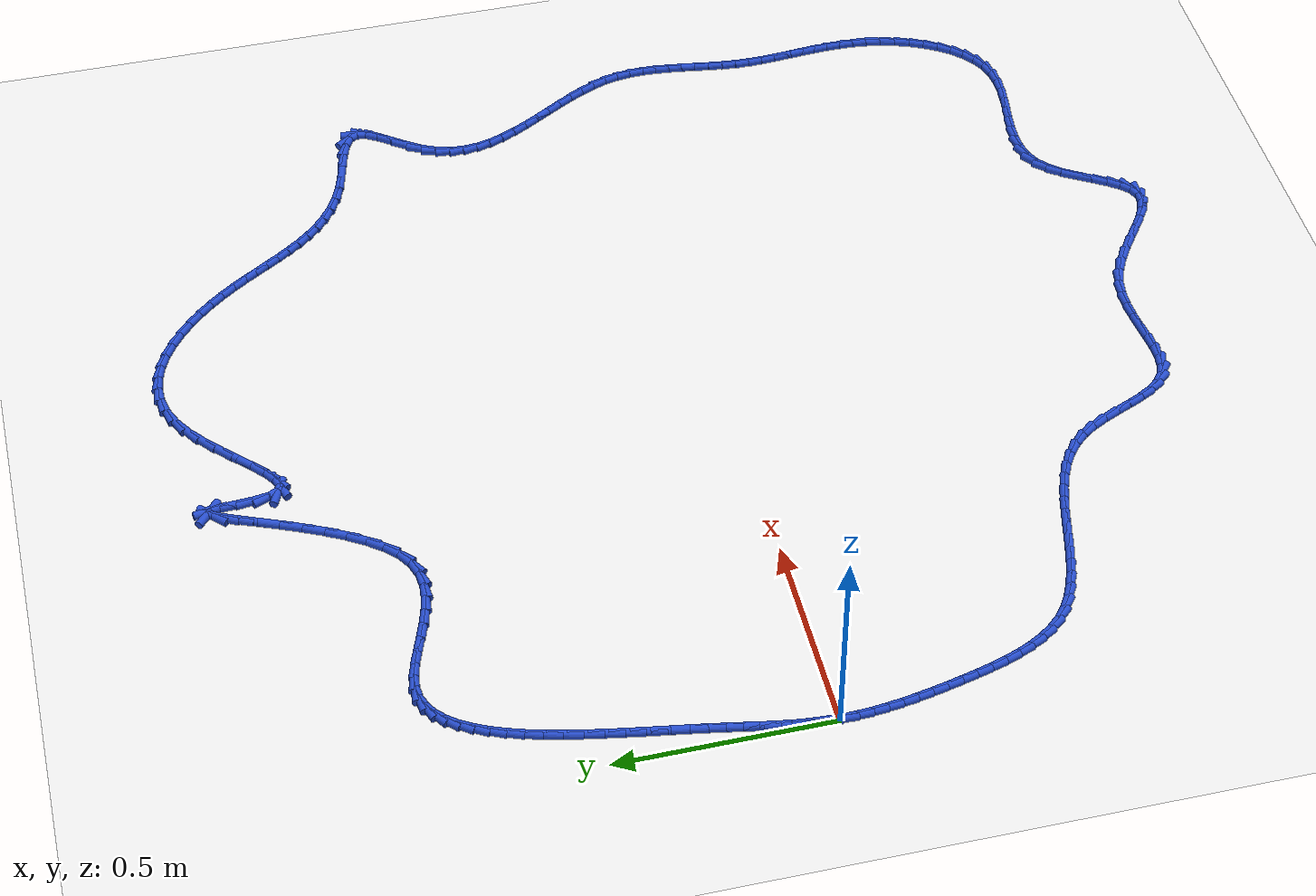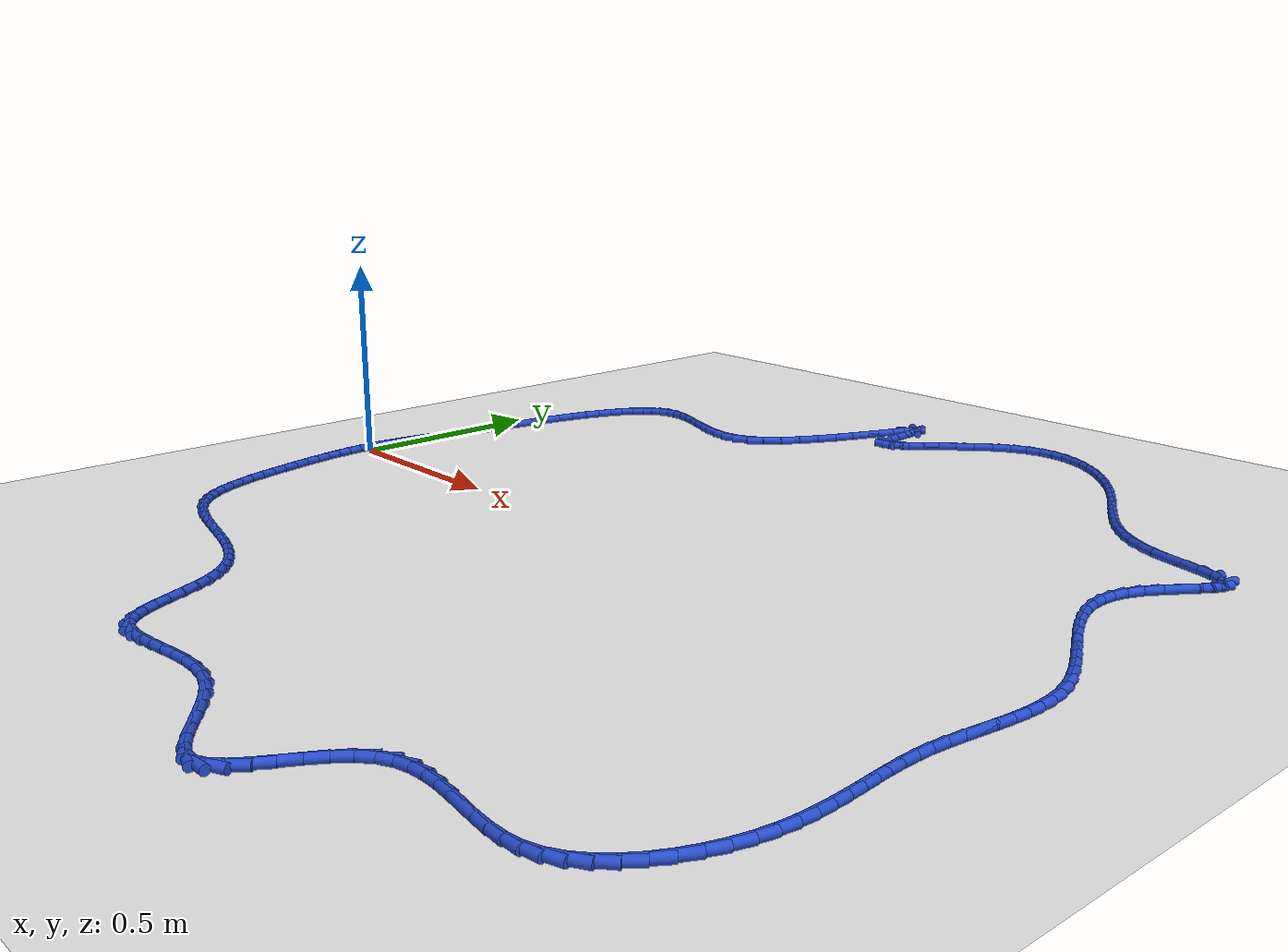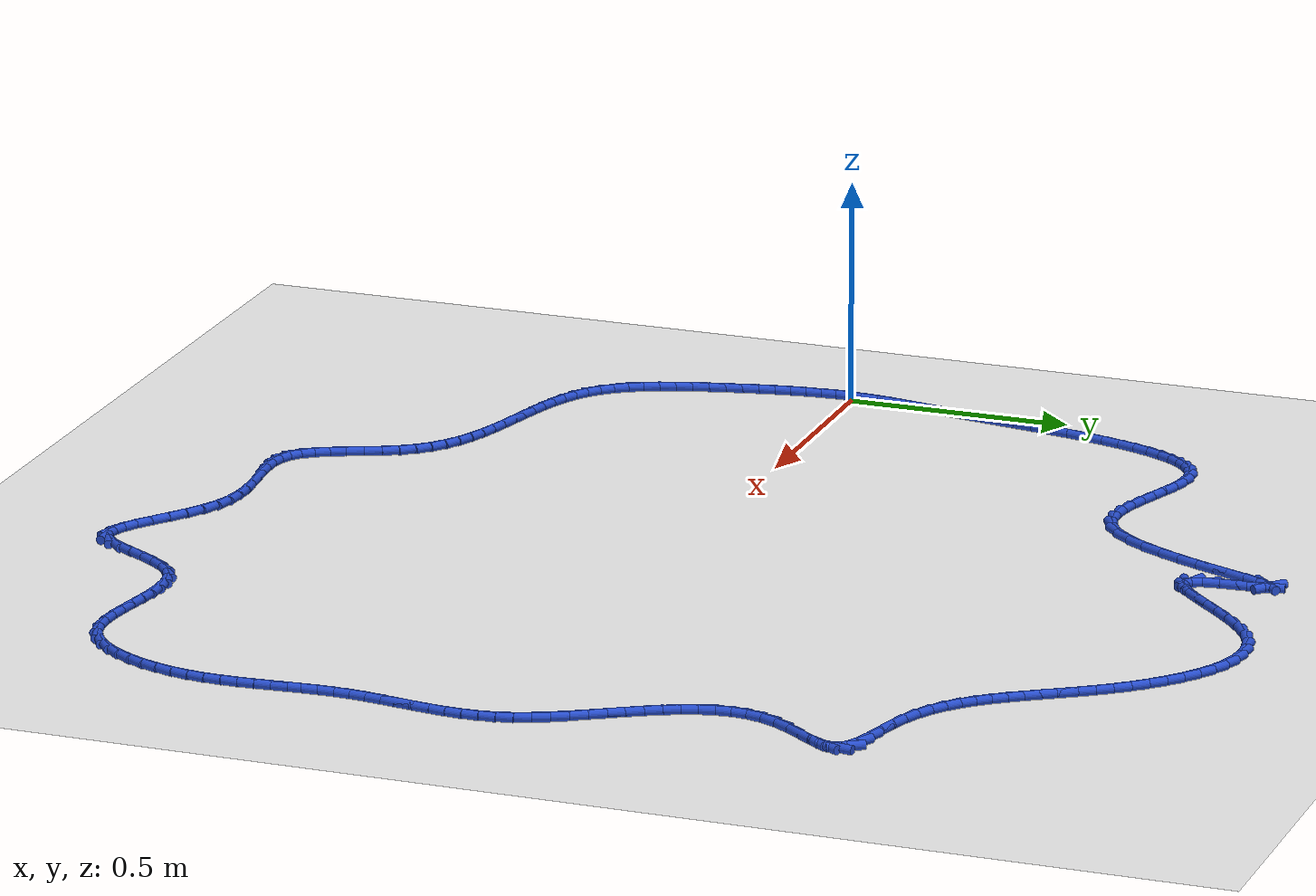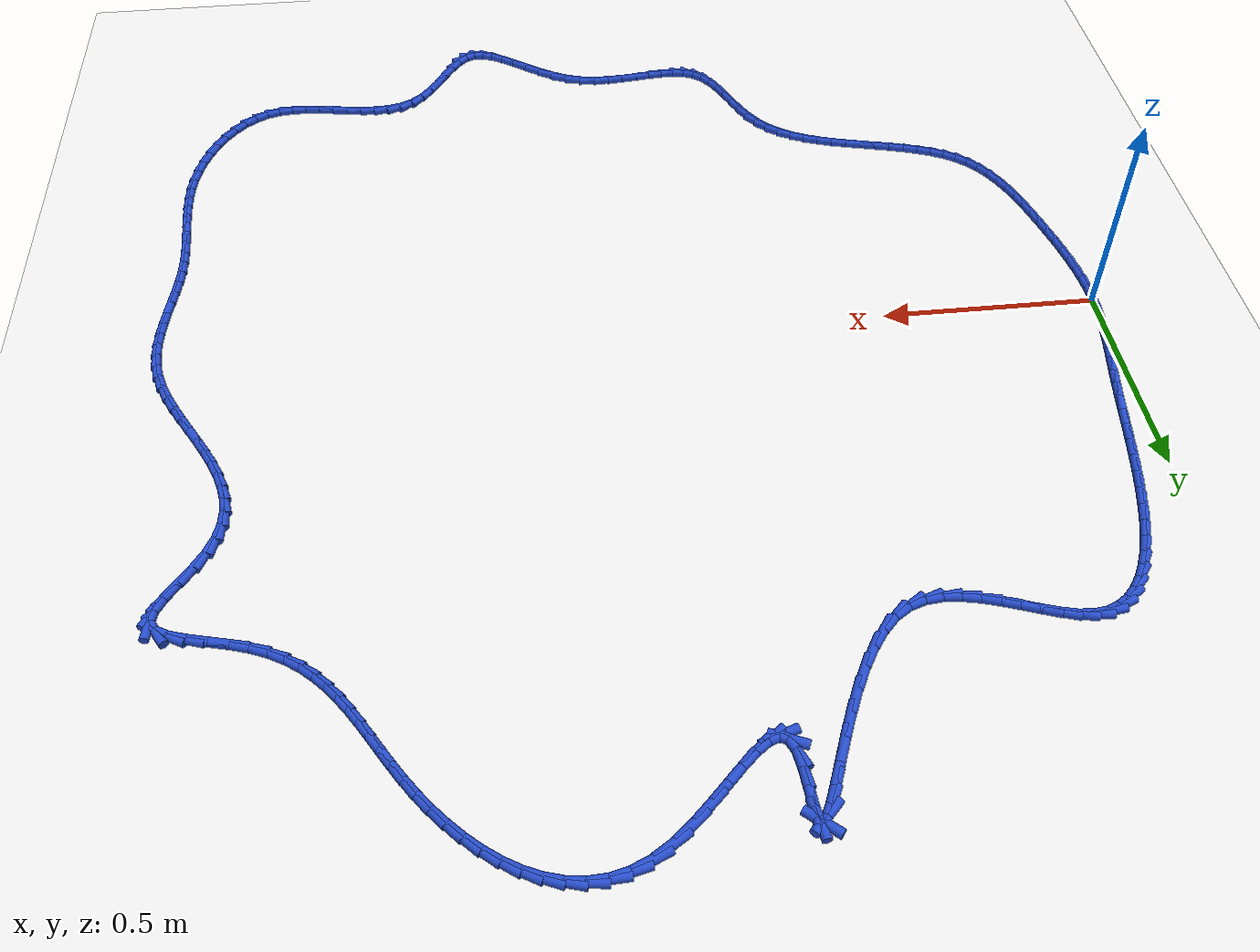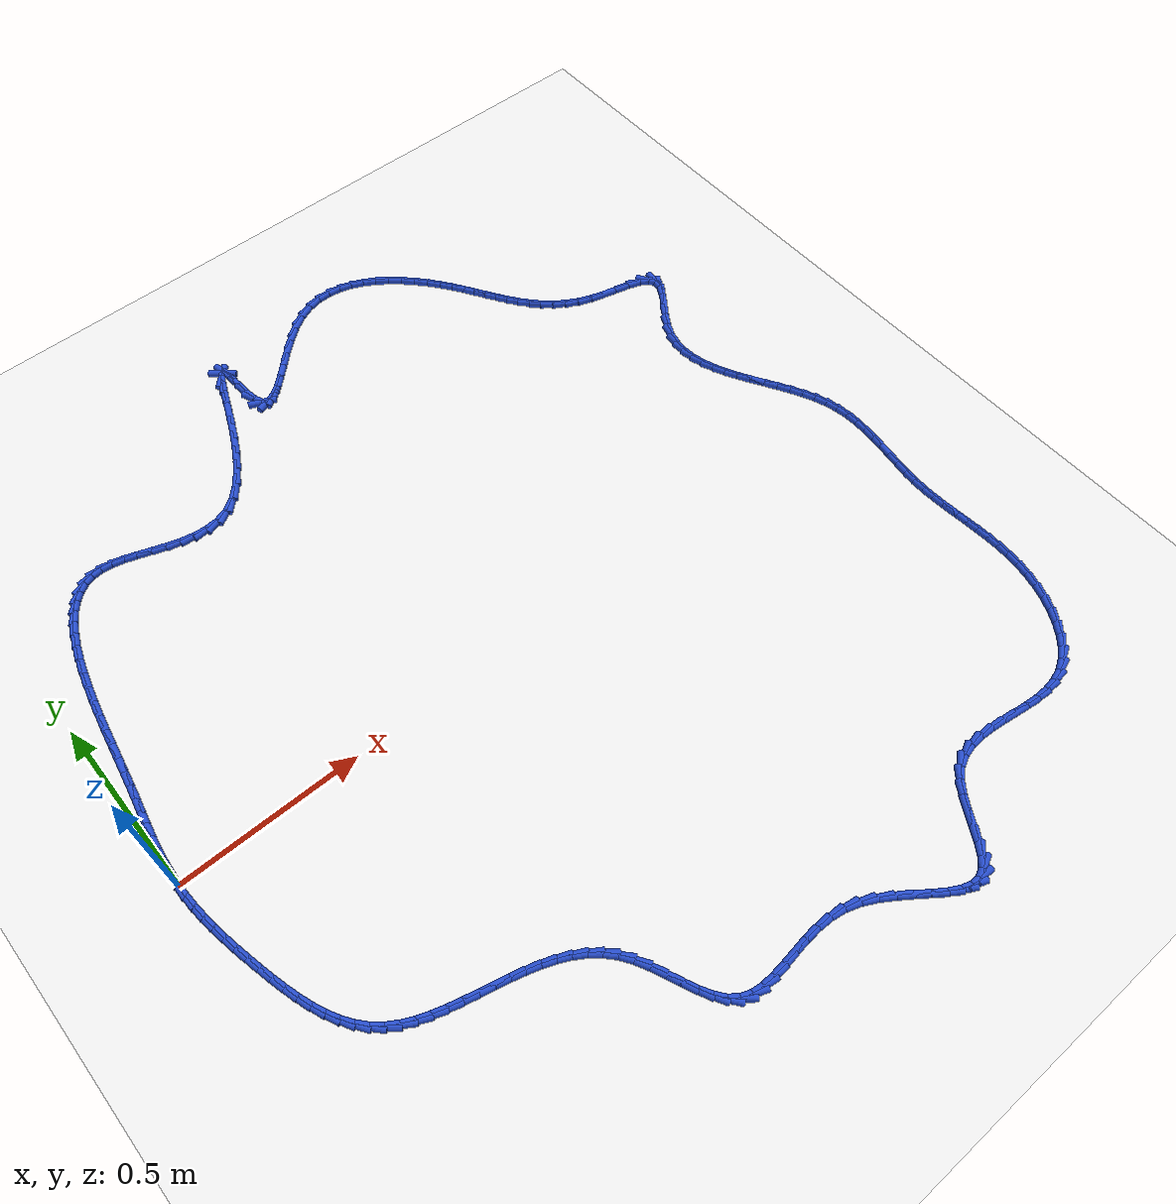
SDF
<sdf version="1.6">
 <world name="default">
  <light name="sun" type="directional">
   <pose>0 0 10 0 -0 0</pose>
   <diffuse>0.8 0.8 0.8 1</diffuse>
   <specular>0.2 0.2 0.2 1</specular>
   <attenuation>
    <range>1000</range>
    <constant>0.9</constant>
    <linear>0.01</linear>
    <quadratic>0.001</quadratic>
   </attenuation>
   <direction>-0.5 0.1 -0.9</direction>
  </light>
  <model name="ground_plane">
   <static>1</static>
   <link name="link">
    <collision name="collision">
     <geometry><plane><normal>0 0 1</normal><size>100 100</size></plane></geometry>
     <surface><friction><ode><mu>100</mu><mu2>50</mu2></ode></friction></surface>
    </collision>
    <visual name="visual">
     <cast_shadows>0</cast_shadows>
     <geometry><plane><normal>0 0 1</normal><size>100 100</size></plane></geometry>
     <material>
      <script><uri>file://media/materials/scripts/gazebo.material</uri><name>Gazebo/WhiteGlow</name></script>
     </material>
    </visual>
   </link>
  </model>
  <gravity>0 0 -9.8</gravity>
  <magnetic_field>6e-06 2.3e-05 -4.2e-05</magnetic_field>
  <atmosphere type="adiabatic"/>
  <physics name="default_physics" default="0" type="ode">
   <max_step_size>0.001</max_step_size>
   <real_time_factor>1</real_time_factor>
   <real_time_update_rate>1000</real_time_update_rate>
  </physics>
  <scene><ambient>0.4 0.4 0.4 1</ambient><background>0.7 0.7 0.7 1</background><shadows>1</shadows></scene>
  <spherical_coordinates>
   <surface_model>EARTH_WGS84</surface_model>
   <latitude_deg>0</latitude_deg>
   <longitude_deg>0</longitude_deg>
   <elevation>0</elevation>
   <heading_deg>0</heading_deg>
  </spherical_coordinates>
  <model name="line">
   <link name="link_0">
    <pose>-2.2551405187698492e-17 -2.7755575615628914e-17 0.01 0 1.57 1.5317768246908199</pose>
    <collision name="collision">
     <geometry><cylinder><radius>0.01</radius><length>0.08</length></cylinder></geometry>
    </collision>
    <visual name="visual">
     <material>
      <script><name>Gazebo/Blue</name><uri>file://media/materials/scripts/gazebo.material</uri></script>
     </material>
     <geometry><cylinder><radius>0.01</radius><length>0.08</length></cylinder></geometry>
    </visual>
   </link>
   <link name="link_1">
    <pose>0.0012909038700178494 0.0330667638219513 0.01 0 1.57 1.4855187835141996</pose>
    <collision name="collision">
     <geometry><cylinder><radius>0.01</radius><length>0.08</length></cylinder></geometry>
    </collision>
    <visual name="visual">
     <material>
      <script><name>Gazebo/Blue</name><uri>file://media/materials/scripts/gazebo.material</uri></script>
     </material>
     <geometry><cylinder><radius>0.01</radius><length>0.08</length></cylinder></geometry>
    </visual>
   </link>
   <link name="link_2">
    <pose>0.004107158025258242 0.06601124007584636 0.01 0 1.57 1.4474695632081067</pose>
    <collision name="collision">
     <geometry><cylinder><radius>0.01</radius><length>0.08</length></cylinder></geometry>
    </collision>
    <visual name="visual">
     <material>
      <script><name>Gazebo/Blue</name><uri>file://media/materials/scripts/gazebo.material</uri></script>
     </material>
     <geometry><cylinder><radius>0.01</radius><length>0.08</length></cylinder></geometry>
    </visual>
   </link>
   <link name="link_3">
    <pose>0.008212593873302988 0.09913138959905807 0.01 0 1.57 1.4184327268474815</pose>
    <collision name="collision">
     <geometry><cylinder><radius>0.01</radius><length>0.08</length></cylinder></geometry>
    </collision>
    <visual name="visual">
     <material>
      <script><name>Gazebo/Blue</name><uri>file://media/materials/scripts/gazebo.material</uri></script>
     </material>
     <geometry><cylinder><radius>0.01</radius><length>0.08</length></cylinder></geometry>
    </visual>
   </link>
   <link name="link_4">
    <pose>0.013371042821733915 0.1327251732289593 0.01 0 1.57 1.3986420646731026</pose>
    <collision name="collision">
     <geometry><cylinder><radius>0.01</radius><length>0.08</length></cylinder></geometry>
    </collision>
    <visual name="visual">
     <material>
      <script><name>Gazebo/Blue</name><uri>file://media/materials/scripts/gazebo.material</uri></script>
     </material>
     <geometry><cylinder><radius>0.01</radius><length>0.08</length></cylinder></geometry>
    </visual>
   </link>
   <link name="link_5">
    <pose>0.019346336278132866 0.16709055180292298 0.01 0 1.57 1.3878507393659656</pose>
    <collision name="collision">
     <geometry><cylinder><radius>0.01</radius><length>0.08</length></cylinder></geometry>
    </collision>
    <visual name="visual">
     <material>
      <script><name>Gazebo/Blue</name><uri>file://media/materials/scripts/gazebo.material</uri></script>
     </material>
     <geometry><cylinder><radius>0.01</radius><length>0.08</length></cylinder></geometry>
    </visual>
   </link>
   <link name="link_6">
    <pose>0.02590230565008166 0.2025254861583219 0.01 0 1.57 1.38544792695444</pose>
    <collision name="collision">
     <geometry><cylinder><radius>0.01</radius><length>0.08</length></cylinder></geometry>
    </collision>
    <visual name="visual">
     <material>
      <script><name>Gazebo/Blue</name><uri>file://media/materials/scripts/gazebo.material</uri></script>
     </material>
     <geometry><cylinder><radius>0.01</radius><length>0.08</length></cylinder></geometry>
    </visual>
   </link>
   <link name="link_7">
    <pose>0.03280278234516214 0.23932793713252892 0.01 0 1.57 1.3905742868097946</pose>
    <collision name="collision">
     <geometry><cylinder><radius>0.01</radius><length>0.08</length></cylinder></geometry>
    </collision>
    <visual name="visual">
     <material>
      <script><name>Gazebo/Blue</name><uri>file://media/materials/scripts/gazebo.material</uri></script>
     </material>
     <geometry><cylinder><radius>0.01</radius><length>0.08</length></cylinder></geometry>
    </visual>
   </link>
   <link name="link_8">
    <pose>0.03981159777095613 0.277795865562917 0.01 0 1.57 1.400694542232976</pose>
    <collision name="collision">
     <geometry><cylinder><radius>0.01</radius><length>0.08</length></cylinder></geometry>
    </collision>
    <visual name="visual">
     <material>
      <script><name>Gazebo/Blue</name><uri>file://media/materials/scripts/gazebo.material</uri></script>
     </material>
     <geometry><cylinder><radius>0.01</radius><length>0.08</length></cylinder></geometry>
    </visual>
   </link>
   <link name="link_9">
    <pose>0.0467401160785049 0.3181338572605922 0.01 0 1.57 1.4072329902828762</pose>
    <collision name="collision">
     <geometry><cylinder><radius>0.01</radius><length>0.08</length></cylinder></geometry>
    </collision>
    <visual name="visual">
     <material>
      <script><name>Gazebo/Blue</name><uri>file://media/materials/scripts/gazebo.material</uri></script>
     </material>
     <geometry><cylinder><radius>0.01</radius><length>0.08</length></cylinder></geometry>
    </visual>
   </link>
   <link name="link_10">
    <pose>0.05365653463498634 0.36004196565418894 0.01 0 1.57 1.4081199562918991</pose>
    <collision name="collision">
     <geometry><cylinder><radius>0.01</radius><length>0.08</length></cylinder></geometry>
    </collision>
    <visual name="visual">
     <material>
      <script><name>Gazebo/Blue</name><uri>file://media/materials/scripts/gazebo.material</uri></script>
     </material>
     <geometry><cylinder><radius>0.01</radius><length>0.08</length></cylinder></geometry>
    </visual>
   </link>
   <link name="link_11">
    <pose>0.06071540281543947 0.40305061119062474 0.01 0 1.57 1.4038046841401903</pose>
    <collision name="collision">
     <geometry><cylinder><radius>0.01</radius><length>0.08</length></cylinder></geometry>
    </collision>
    <visual name="visual">
     <material>
      <script><name>Gazebo/Blue</name><uri>file://media/materials/scripts/gazebo.material</uri></script>
     </material>
     <geometry><cylinder><radius>0.01</radius><length>0.08</length></cylinder></geometry>
    </visual>
   </link>
   <link name="link_12">
    <pose>0.06807133447739407 0.446690087645099 0.01 0 1.57 1.3943956237105248</pose>
    <collision name="collision">
     <geometry><cylinder><radius>0.01</radius><length>0.08</length></cylinder></geometry>
    </collision>
    <visual name="visual">
     <material>
      <script><name>Gazebo/Blue</name><uri>file://media/materials/scripts/gazebo.material</uri></script>
     </material>
     <geometry><cylinder><radius>0.01</radius><length>0.08</length></cylinder></geometry>
    </visual>
   </link>
   <link name="link_13">
    <pose>0.07587894347837983 0.4904906887928109 0.01 0 1.57 1.3796985251317877</pose>
    <collision name="collision">
     <geometry><cylinder><radius>0.01</radius><length>0.08</length></cylinder></geometry>
    </collision>
    <visual name="visual">
     <material>
      <script><name>Gazebo/Blue</name><uri>file://media/materials/scripts/gazebo.material</uri></script>
     </material>
     <geometry><cylinder><radius>0.01</radius><length>0.08</length></cylinder></geometry>
    </visual>
   </link>
   <link name="link_14">
    <pose>0.08429284367592652 0.53398270840896 0.01 0 1.57 1.3592136734023892</pose>
    <collision name="collision">
     <geometry><cylinder><radius>0.01</radius><length>0.08</length></cylinder></geometry>
    </collision>
    <visual name="visual">
     <material>
      <script><name>Gazebo/Blue</name><uri>file://media/materials/scripts/gazebo.material</uri></script>
     </material>
     <geometry><cylinder><radius>0.01</radius><length>0.08</length></cylinder></geometry>
    </visual>
   </link>
   <link name="link_15">
    <pose>0.0934676489275639 0.5766964402687462 0.01 0 1.57 1.3320944818567027</pose>
    <collision name="collision">
     <geometry><cylinder><radius>0.01</radius><length>0.08</length></cylinder></geometry>
    </collision>
    <visual name="visual">
     <material>
      <script><name>Gazebo/Blue</name><uri>file://media/materials/scripts/gazebo.material</uri></script>
     </material>
     <geometry><cylinder><radius>0.01</radius><length>0.08</length></cylinder></geometry>
    </visual>
   </link>
   <link name="link_16">
    <pose>0.10355797309082168 0.6181621781473685 0.01 0 1.57 1.2970644085488432</pose>
    <collision name="collision">
     <geometry><cylinder><radius>0.01</radius><length>0.08</length></cylinder></geometry>
    </collision>
    <visual name="visual">
     <material>
      <script><name>Gazebo/Blue</name><uri>file://media/materials/scripts/gazebo.material</uri></script>
     </material>
     <geometry><cylinder><radius>0.01</radius><length>0.08</length></cylinder></geometry>
    </visual>
   </link>
   <link name="link_17">
    <pose>0.11471843002322968 0.6579102158200267 0.01 0 1.57 1.2522841872776282</pose>
    <collision name="collision">
     <geometry><cylinder><radius>0.01</radius><length>0.08</length></cylinder></geometry>
    </collision>
    <visual name="visual">
     <material>
      <script><name>Gazebo/Blue</name><uri>file://media/materials/scripts/gazebo.material</uri></script>
     </material>
     <geometry><cylinder><radius>0.01</radius><length>0.08</length></cylinder></geometry>
    </visual>
   </link>
   <link name="link_18">
    <pose>0.12710363358231758 0.6954708470619201 0.01 0 1.57 1.195161145644118</pose>
    <collision name="collision">
     <geometry><cylinder><radius>0.01</radius><length>0.08</length></cylinder></geometry>
    </collision>
    <visual name="visual">
     <material>
      <script><name>Gazebo/Blue</name><uri>file://media/materials/scripts/gazebo.material</uri></script>
     </material>
     <geometry><cylinder><radius>0.01</radius><length>0.08</length></cylinder></geometry>
    </visual>
   </link>
   <link name="link_19">
    <pose>0.14086819762561512 0.7303743656482482 0.01 0 1.57 1.1221075758826076</pose>
    <collision name="collision">
     <geometry><cylinder><radius>0.01</radius><length>0.08</length></cylinder></geometry>
    </collision>
    <visual name="visual">
     <material>
      <script><name>Gazebo/Blue</name><uri>file://media/materials/scripts/gazebo.material</uri></script>
     </material>
     <geometry><cylinder><radius>0.01</radius><length>0.08</length></cylinder></geometry>
    </visual>
   </link>
   <link name="link_20">
    <pose>0.15616673601065204 0.7621510653542103 0.01 0 1.57 1.0283174920021094</pose>
    <collision name="collision">
     <geometry><cylinder><radius>0.01</radius><length>0.08</length></cylinder></geometry>
    </collision>
    <visual name="visual">
     <material>
      <script><name>Gazebo/Blue</name><uri>file://media/materials/scripts/gazebo.material</uri></script>
     </material>
     <geometry><cylinder><radius>0.01</radius><length>0.08</length></cylinder></geometry>
    </visual>
   </link>
   <link name="link_21">
    <pose>0.173153862594958 0.7903312399550055 0.01 0 1.57 0.9078171462795516</pose>
    <collision name="collision">
     <geometry><cylinder><radius>0.01</radius><length>0.08</length></cylinder></geometry>
    </collision>
    <visual name="visual">
     <material>
      <script><name>Gazebo/Blue</name><uri>file://media/materials/scripts/gazebo.material</uri></script>
     </material>
     <geometry><cylinder><radius>0.01</radius><length>0.08</length></cylinder></geometry>
    </visual>
   </link>
   <link name="link_22">
    <pose>0.19198419123606292 0.8144451832258341 0.01 0 1.57 0.7544687092185683</pose>
    <collision name="collision">
     <geometry><cylinder><radius>0.01</radius><length>0.08</length></cylinder></geometry>
    </collision>
    <visual name="visual">
     <material>
      <script><name>Gazebo/Blue</name><uri>file://media/materials/scripts/gazebo.material</uri></script>
     </material>
     <geometry><cylinder><radius>0.01</radius><length>0.08</length></cylinder></geometry>
    </visual>
   </link>
   <link name="link_23">
    <pose>0.2128123357914965 0.8340231889418955 0.01 0 1.57 0.5651281748237728</pose>
    <collision name="collision">
     <geometry><cylinder><radius>0.01</radius><length>0.08</length></cylinder></geometry>
    </collision>
    <visual name="visual">
     <material>
      <script><name>Gazebo/Blue</name><uri>file://media/materials/scripts/gazebo.material</uri></script>
     </material>
     <geometry><cylinder><radius>0.01</radius><length>0.08</length></cylinder></geometry>
    </visual>
   </link>
   <link name="link_24">
    <pose>0.23579291011878845 0.8485955508783887 0.01 0 1.57 0.345326940844086</pose>
    <collision name="collision">
     <geometry><cylinder><radius>0.01</radius><length>0.08</length></cylinder></geometry>
    </collision>
    <visual name="visual">
     <material>
      <script><name>Gazebo/Blue</name><uri>file://media/materials/scripts/gazebo.material</uri></script>
     </material>
     <geometry><cylinder><radius>0.01</radius><length>0.08</length></cylinder></geometry>
    </visual>
   </link>
   <link name="link_25">
    <pose>0.2610805280754685 0.8576925628105132 0.01 0 1.57 0.11310220264081204</pose>
    <collision name="collision">
     <geometry><cylinder><radius>0.01</radius><length>0.08</length></cylinder></geometry>
    </collision>
    <visual name="visual">
     <material>
      <script><name>Gazebo/Blue</name><uri>file://media/materials/scripts/gazebo.material</uri></script>
     </material>
     <geometry><cylinder><radius>0.01</radius><length>0.08</length></cylinder></geometry>
    </visual>
   </link>
   <link name="link_26">
    <pose>0.2888298035190664 0.8608445185134688 0.01 0 1.57 -0.09740739574681635</pose>
    <collision name="collision">
     <geometry><cylinder><radius>0.01</radius><length>0.08</length></cylinder></geometry>
    </collision>
    <visual name="visual">
     <material>
      <script><name>Gazebo/Blue</name><uri>file://media/materials/scripts/gazebo.material</uri></script>
     </material>
     <geometry><cylinder><radius>0.01</radius><length>0.08</length></cylinder></geometry>
    </visual>
   </link>
   <link name="link_27">
    <pose>0.31910952958864747 0.8578856853272954 0.01 0 1.57 -0.23689055770752723</pose>
    <collision name="collision">
     <geometry><cylinder><radius>0.01</radius><length>0.08</length></cylinder></geometry>
    </collision>
    <visual name="visual">
     <material>
      <script><name>Gazebo/Blue</name><uri>file://media/materials/scripts/gazebo.material</uri></script>
     </material>
     <geometry><cylinder><radius>0.01</radius><length>0.08</length></cylinder></geometry>
    </visual>
   </link>
   <link name="link_28">
    <pose>0.3515953520328002 0.8500428429821543 0.01 0 1.57 -0.3134043362732711</pose>
    <collision name="collision">
     <geometry><cylinder><radius>0.01</radius><length>0.08</length></cylinder></geometry>
    </collision>
    <visual name="visual">
     <material>
      <script><name>Gazebo/Blue</name><uri>file://media/materials/scripts/gazebo.material</uri></script>
     </material>
     <geometry><cylinder><radius>0.01</radius><length>0.08</length></cylinder></geometry>
    </visual>
   </link>
   <link name="link_29">
    <pose>0.38585040437144963 0.8389412850385152 0.01 0 1.57 -0.34365080850688107</pose>
    <collision name="collision">
     <geometry><cylinder><radius>0.01</radius><length>0.08</length></cylinder></geometry>
    </collision>
    <visual name="visual">
     <material>
      <script><name>Gazebo/Blue</name><uri>file://media/materials/scripts/gazebo.material</uri></script>
     </material>
     <geometry><cylinder><radius>0.01</radius><length>0.08</length></cylinder></geometry>
    </visual>
   </link>
   <link name="link_30">
    <pose>0.421437811047149 0.8262063372085358 0.01 0 1.57 -0.3360398405132245</pose>
    <collision name="collision">
     <geometry><cylinder><radius>0.01</radius><length>0.08</length></cylinder></geometry>
    </collision>
    <visual name="visual">
     <material>
      <script><name>Gazebo/Blue</name><uri>file://media/materials/scripts/gazebo.material</uri></script>
     </material>
     <geometry><cylinder><radius>0.01</radius><length>0.08</length></cylinder></geometry>
    </visual>
   </link>
   <link name="link_31">
    <pose>0.45792069650245176 0.813463325204375 0.01 0 1.57 -0.2925318861233845</pose>
    <collision name="collision">
     <geometry><cylinder><radius>0.01</radius><length>0.08</length></cylinder></geometry>
    </collision>
    <visual name="visual">
     <material>
      <script><name>Gazebo/Blue</name><uri>file://media/materials/scripts/gazebo.material</uri></script>
     </material>
     <geometry><cylinder><radius>0.01</radius><length>0.08</length></cylinder></geometry>
    </visual>
   </link>
   <link name="link_32">
    <pose>0.4948621851799112 0.8023375747381903 0.01 0 1.57 -0.2101224769590258</pose>
    <collision name="collision">
     <geometry><cylinder><radius>0.01</radius><length>0.08</length></cylinder></geometry>
    </collision>
    <visual name="visual">
     <material>
      <script><name>Gazebo/Blue</name><uri>file://media/materials/scripts/gazebo.material</uri></script>
     </material>
     <geometry><cylinder><radius>0.01</radius><length>0.08</length></cylinder></geometry>
    </visual>
   </link>
   <link name="link_33">
    <pose>0.5318254015220802 0.7944544115221401 0.01 0 1.57 -0.0823145292716578</pose>
    <collision name="collision">
     <geometry><cylinder><radius>0.01</radius><length>0.08</length></cylinder></geometry>
    </collision>
    <visual name="visual">
     <material>
      <script><name>Gazebo/Blue</name><uri>file://media/materials/scripts/gazebo.material</uri></script>
     </material>
     <geometry><cylinder><radius>0.01</radius><length>0.08</length></cylinder></geometry>
    </visual>
   </link>
   <link name="link_34">
    <pose>0.5683734699715125 0.7914391612683831 0.01 0 1.57 0.09712686248858758</pose>
    <collision name="collision">
     <geometry><cylinder><radius>0.01</radius><length>0.08</length></cylinder></geometry>
    </collision>
    <visual name="visual">
     <material>
      <script><name>Gazebo/Blue</name><uri>file://media/materials/scripts/gazebo.material</uri></script>
     </material>
     <geometry><cylinder><radius>0.01</radius><length>0.08</length></cylinder></geometry>
    </visual>
   </link>
   <link name="link_35">
    <pose>0.6040695149707613 0.7949171496890765 0.01 0 1.57 0.32508200979457447</pose>
    <collision name="collision">
     <geometry><cylinder><radius>0.01</radius><length>0.08</length></cylinder></geometry>
    </collision>
    <visual name="visual">
     <material>
      <script><name>Gazebo/Blue</name><uri>file://media/materials/scripts/gazebo.material</uri></script>
     </material>
     <geometry><cylinder><radius>0.01</radius><length>0.08</length></cylinder></geometry>
    </visual>
   </link>
   <link name="link_36">
    <pose>0.6384766609623798 0.8065137024963789 0.01 0 1.57 0.5771828616528781</pose>
    <collision name="collision">
     <geometry><cylinder><radius>0.01</radius><length>0.08</length></cylinder></geometry>
    </collision>
    <visual name="visual">
     <material>
      <script><name>Gazebo/Blue</name><uri>file://media/materials/scripts/gazebo.material</uri></script>
     </material>
     <geometry><cylinder><radius>0.01</radius><length>0.08</length></cylinder></geometry>
    </visual>
   </link>
   <link name="link_37">
    <pose>0.6711639082527683 0.8277979863464503 0.01 0 1.57 0.7877276035489035</pose>
    <collision name="collision">
     <geometry><cylinder><radius>0.01</radius><length>0.08</length></cylinder></geometry>
    </collision>
    <visual name="visual">
     <material>
      <script><name>Gazebo/Blue</name><uri>file://media/materials/scripts/gazebo.material</uri></script>
     </material>
     <geometry><cylinder><radius>0.01</radius><length>0.08</length></cylinder></geometry>
    </visual>
   </link>
   <link name="link_38">
    <pose>0.7018765675512489 0.8586540665983288 0.01 0 1.57 0.9288717631295644</pose>
    <collision name="collision">
     <geometry><cylinder><radius>0.01</radius><length>0.08</length></cylinder></geometry>
    </collision>
    <visual name="visual">
     <material>
      <script><name>Gazebo/Blue</name><uri>file://media/materials/scripts/gazebo.material</uri></script>
     </material>
     <geometry><cylinder><radius>0.01</radius><length>0.08</length></cylinder></geometry>
    </visual>
   </link>
   <link name="link_39">
    <pose>0.7305627065767368 0.8970281416774734 0.01 0 1.57 1.024009746363108</pose>
    <collision name="collision">
     <geometry><cylinder><radius>0.01</radius><length>0.08</length></cylinder></geometry>
    </collision>
    <visual name="visual">
     <material>
      <script><name>Gazebo/Blue</name><uri>file://media/materials/scripts/gazebo.material</uri></script>
     </material>
     <geometry><cylinder><radius>0.01</radius><length>0.08</length></cylinder></geometry>
    </visual>
   </link>
   <link name="link_40">
    <pose>0.7571815906426184 0.9407593880715843 0.01 0 1.57 1.0894580405173635</pose>
    <collision name="collision">
     <geometry><cylinder><radius>0.01</radius><length>0.08</length></cylinder></geometry>
    </collision>
    <visual name="visual">
     <material>
      <script><name>Gazebo/Blue</name><uri>file://media/materials/scripts/gazebo.material</uri></script>
     </material>
     <geometry><cylinder><radius>0.01</radius><length>0.08</length></cylinder></geometry>
    </visual>
   </link>
   <link name="link_41">
    <pose>0.7816924850622796 0.9876869822683609 0.01 0 1.57 1.1345222314347991</pose>
    <collision name="collision">
     <geometry><cylinder><radius>0.01</radius><length>0.08</length></cylinder></geometry>
    </collision>
    <visual name="visual">
     <material>
      <script><name>Gazebo/Blue</name><uri>file://media/materials/scripts/gazebo.material</uri></script>
     </material>
     <geometry><cylinder><radius>0.01</radius><length>0.08</length></cylinder></geometry>
    </visual>
   </link>
   <link name="link_42">
    <pose>0.8040546551491081 1.0356501007555048 0.01 0 1.57 1.164113733062502</pose>
    <collision name="collision">
     <geometry><cylinder><radius>0.01</radius><length>0.08</length></cylinder></geometry>
    </collision>
    <visual name="visual">
     <material>
      <script><name>Gazebo/Blue</name><uri>file://media/materials/scripts/gazebo.material</uri></script>
     </material>
     <geometry><cylinder><radius>0.01</radius><length>0.08</length></cylinder></geometry>
    </visual>
   </link>
   <link name="link_43">
    <pose>0.824227366216489 1.0824879200207147 0.01 0 1.57 1.1800034588505761</pose>
    <collision name="collision">
     <geometry><cylinder><radius>0.01</radius><length>0.08</length></cylinder></geometry>
    </collision>
    <visual name="visual">
     <material>
      <script><name>Gazebo/Blue</name><uri>file://media/materials/scripts/gazebo.material</uri></script>
     </material>
     <geometry><cylinder><radius>0.01</radius><length>0.08</length></cylinder></geometry>
    </visual>
   </link>
   <link name="link_44">
    <pose>0.8421698835778095 1.126039616551692 0.01 0 1.57 1.1806067709805428</pose>
    <collision name="collision">
     <geometry><cylinder><radius>0.01</radius><length>0.08</length></cylinder></geometry>
    </collision>
    <visual name="visual">
     <material>
      <script><name>Gazebo/Blue</name><uri>file://media/materials/scripts/gazebo.material</uri></script>
     </material>
     <geometry><cylinder><radius>0.01</radius><length>0.08</length></cylinder></geometry>
    </visual>
   </link>
   <link name="link_45">
    <pose>0.8578414725464556 1.1641443668361355 0.01 0 1.57 1.1579044330749586</pose>
    <collision name="collision">
     <geometry><cylinder><radius>0.01</radius><length>0.08</length></cylinder></geometry>
    </collision>
    <visual name="visual">
     <material>
      <script><name>Gazebo/Blue</name><uri>file://media/materials/scripts/gazebo.material</uri></script>
     </material>
     <geometry><cylinder><radius>0.01</radius><length>0.08</length></cylinder></geometry>
    </visual>
   </link>
   <link name="link_46">
    <pose>0.8712013984358135 1.1946413473617459 0.01 0 1.57 1.0826289765320969</pose>
    <collision name="collision">
     <geometry><cylinder><radius>0.01</radius><length>0.08</length></cylinder></geometry>
    </collision>
    <visual name="visual">
     <material>
      <script><name>Gazebo/Blue</name><uri>file://media/materials/scripts/gazebo.material</uri></script>
     </material>
     <geometry><cylinder><radius>0.01</radius><length>0.08</length></cylinder></geometry>
    </visual>
   </link>
   <link name="link_47">
    <pose>0.8822089265592699 1.2153697346162229 0.01 0 1.57 0.7959973713069253</pose>
    <collision name="collision">
     <geometry><cylinder><radius>0.01</radius><length>0.08</length></cylinder></geometry>
    </collision>
    <visual name="visual">
     <material>
      <script><name>Gazebo/Blue</name><uri>file://media/materials/scripts/gazebo.material</uri></script>
     </material>
     <geometry><cylinder><radius>0.01</radius><length>0.08</length></cylinder></geometry>
    </visual>
   </link>
   <link name="link_48">
    <pose>0.890823322230211 1.224168705087267 0.01 0 1.57 -0.7080359290475473</pose>
    <collision name="collision">
     <geometry><cylinder><radius>0.01</radius><length>0.08</length></cylinder></geometry>
    </collision>
    <visual name="visual">
     <material>
      <script><name>Gazebo/Blue</name><uri>file://media/materials/scripts/gazebo.material</uri></script>
     </material>
     <geometry><cylinder><radius>0.01</radius><length>0.08</length></cylinder></geometry>
    </visual>
   </link>
   <link name="link_49">
    <pose>0.8970038507620233 1.2188774352625782 0.01 0 1.57 -1.3988786667722337</pose>
    <collision name="collision">
     <geometry><cylinder><radius>0.01</radius><length>0.08</length></cylinder></geometry>
    </collision>
    <visual name="visual">
     <material>
      <script><name>Gazebo/Blue</name><uri>file://media/materials/scripts/gazebo.material</uri></script>
     </material>
     <geometry><cylinder><radius>0.01</radius><length>0.08</length></cylinder></geometry>
    </visual>
   </link>
   <link name="link_50">
    <pose>0.9007281348322297 1.1974280953967282 0.01 0 1.57 -1.510663499018459</pose>
    <collision name="collision">
     <geometry><cylinder><radius>0.01</radius><length>0.08</length></cylinder></geometry>
    </collision>
    <visual name="visual">
     <material>
      <script><name>Gazebo/Blue</name><uri>file://media/materials/scripts/gazebo.material</uri></script>
     </material>
     <geometry><cylinder><radius>0.01</radius><length>0.08</length></cylinder></geometry>
    </visual>
   </link>
   <link name="link_51">
    <pose>0.9028496704141361 1.1621898084827669 0.01 0 1.57 -1.5061326454913322</pose>
    <collision name="collision">
     <geometry><cylinder><radius>0.01</radius><length>0.08</length></cylinder></geometry>
    </collision>
    <visual name="visual">
     <material>
      <script><name>Gazebo/Blue</name><uri>file://media/materials/scripts/gazebo.material</uri></script>
     </material>
     <geometry><cylinder><radius>0.01</radius><length>0.08</length></cylinder></geometry>
    </visual>
   </link>
   <link name="link_52">
    <pose>0.9054636557636966 1.1218218474360009 0.01 0 1.57 -1.4261619346519163</pose>
    <collision name="collision">
     <geometry><cylinder><radius>0.01</radius><length>0.08</length></cylinder></geometry>
    </collision>
    <visual name="visual">
     <material>
      <script><name>Gazebo/Blue</name><uri>file://media/materials/scripts/gazebo.material</uri></script>
     </material>
     <geometry><cylinder><radius>0.01</radius><length>0.08</length></cylinder></geometry>
    </visual>
   </link>
   <link name="link_53">
    <pose>0.9107596176778908 1.085461329718922 0.01 0 1.57 -1.1622807201396543</pose>
    <collision name="collision">
     <geometry><cylinder><radius>0.01</radius><length>0.08</length></cylinder></geometry>
    </collision>
    <visual name="visual">
     <material>
      <script><name>Gazebo/Blue</name><uri>file://media/materials/scripts/gazebo.material</uri></script>
     </material>
     <geometry><cylinder><radius>0.01</radius><length>0.08</length></cylinder></geometry>
    </visual>
   </link>
   <link name="link_54">
    <pose>0.9208852109740544 1.0620694318032669 0.01 0 1.57 -0.406060123291478</pose>
    <collision name="collision">
     <geometry><cylinder><radius>0.01</radius><length>0.08</length></cylinder></geometry>
    </collision>
    <visual name="visual">
     <material>
      <script><name>Gazebo/Blue</name><uri>file://media/materials/scripts/gazebo.material</uri></script>
     </material>
     <geometry><cylinder><radius>0.01</radius><length>0.08</length></cylinder></geometry>
    </visual>
   </link>
   <link name="link_55">
    <pose>0.9367161606544918 1.0552628350177926 0.01 0 1.57 0.3316702548695326</pose>
    <collision name="collision">
     <geometry><cylinder><radius>0.01</radius><length>0.08</length></cylinder></geometry>
    </collision>
    <visual name="visual">
     <material>
      <script><name>Gazebo/Blue</name><uri>file://media/materials/scripts/gazebo.material</uri></script>
     </material>
     <geometry><cylinder><radius>0.01</radius><length>0.08</length></cylinder></geometry>
    </visual>
   </link>
   <link name="link_56">
    <pose>0.9576565449408468 1.0624745390301613 0.01 0 1.57 0.6253300588567127</pose>
    <collision name="collision">
     <geometry><cylinder><radius>0.01</radius><length>0.08</length></cylinder></geometry>
    </collision>
    <visual name="visual">
     <material>
      <script><name>Gazebo/Blue</name><uri>file://media/materials/scripts/gazebo.material</uri></script>
     </material>
     <geometry><cylinder><radius>0.01</radius><length>0.08</length></cylinder></geometry>
    </visual>
   </link>
   <link name="link_57">
    <pose>0.9830283601473826 1.08079264526747 0.01 0 1.57 0.7384748070590244</pose>
    <collision name="collision">
     <geometry><cylinder><radius>0.01</radius><length>0.08</length></cylinder></geometry>
    </collision>
    <visual name="visual">
     <material>
      <script><name>Gazebo/Blue</name><uri>file://media/materials/scripts/gazebo.material</uri></script>
     </material>
     <geometry><cylinder><radius>0.01</radius><length>0.08</length></cylinder></geometry>
    </visual>
   </link>
   <link name="link_58">
    <pose>1.0121536025883622 1.107305255156816 0.01 0 1.57 0.7790626682001327</pose>
    <collision name="collision">
     <geometry><cylinder><radius>0.01</radius><length>0.08</length></cylinder></geometry>
    </collision>
    <visual name="visual">
     <material>
      <script><name>Gazebo/Blue</name><uri>file://media/materials/scripts/gazebo.material</uri></script>
     </material>
     <geometry><cylinder><radius>0.01</radius><length>0.08</length></cylinder></geometry>
    </visual>
   </link>
   <link name="link_59">
    <pose>1.044354268578048 1.1391004701252971 0.01 0 1.57 0.7791134992978405</pose>
    <collision name="collision">
     <geometry><cylinder><radius>0.01</radius><length>0.08</length></cylinder></geometry>
    </collision>
    <visual name="visual">
     <material>
      <script><name>Gazebo/Blue</name><uri>file://media/materials/scripts/gazebo.material</uri></script>
     </material>
     <geometry><cylinder><radius>0.01</radius><length>0.08</length></cylinder></geometry>
    </visual>
   </link>
   <link name="link_60">
    <pose>1.0789523544307038 1.17326639160001 0.01 0 1.57 0.7469172156542614</pose>
    <collision name="collision">
     <geometry><cylinder><radius>0.01</radius><length>0.08</length></cylinder></geometry>
    </collision>
    <visual name="visual">
     <material>
      <script><name>Gazebo/Blue</name><uri>file://media/materials/scripts/gazebo.material</uri></script>
     </material>
     <geometry><cylinder><radius>0.01</radius><length>0.08</length></cylinder></geometry>
    </visual>
   </link>
   <link name="link_61">
    <pose>1.1152698564605923 1.2068911210080524 0.01 0 1.57 0.679367325697816</pose>
    <collision name="collision">
     <geometry><cylinder><radius>0.01</radius><length>0.08</length></cylinder></geometry>
    </collision>
    <visual name="visual">
     <material>
      <script><name>Gazebo/Blue</name><uri>file://media/materials/scripts/gazebo.material</uri></script>
     </material>
     <geometry><cylinder><radius>0.01</radius><length>0.08</length></cylinder></geometry>
    </visual>
   </link>
   <link name="link_62">
    <pose>1.1526287709819751 1.2370627597765207 0.01 0 1.57 0.5632754730702765</pose>
    <collision name="collision">
     <geometry><cylinder><radius>0.01</radius><length>0.08</length></cylinder></geometry>
    </collision>
    <visual name="visual">
     <material>
      <script><name>Gazebo/Blue</name><uri>file://media/materials/scripts/gazebo.material</uri></script>
     </material>
     <geometry><cylinder><radius>0.01</radius><length>0.08</length></cylinder></geometry>
    </visual>
   </link>
   <link name="link_63">
    <pose>1.1903535713489202 1.2608867970132862 0.01 0 1.57 0.3988650520871717</pose>
    <collision name="collision">
     <geometry><cylinder><radius>0.01</radius><length>0.08</length></cylinder></geometry>
    </collision>
    <visual name="visual">
     <material>
      <script><name>Gazebo/Blue</name><uri>file://media/materials/scripts/gazebo.material</uri></script>
     </material>
     <geometry><cylinder><radius>0.01</radius><length>0.08</length></cylinder></geometry>
    </visual>
   </link>
   <link name="link_64">
    <pose>1.2279486194932527 1.2767314569509989 0.01 0 1.57 0.21986535917009523</pose>
    <collision name="collision">
     <geometry><cylinder><radius>0.01</radius><length>0.08</length></cylinder></geometry>
    </collision>
    <visual name="visual">
     <material>
      <script><name>Gazebo/Blue</name><uri>file://media/materials/scripts/gazebo.material</uri></script>
     </material>
     <geometry><cylinder><radius>0.01</radius><length>0.08</length></cylinder></geometry>
    </visual>
   </link>
   <link name="link_65">
    <pose>1.2652167443375506 1.285060064898213 0.01 0 1.57 0.040042610725634774</pose>
    <collision name="collision">
     <geometry><cylinder><radius>0.01</radius><length>0.08</length></cylinder></geometry>
    </collision>
    <visual name="visual">
     <material>
      <script><name>Gazebo/Blue</name><uri>file://media/materials/scripts/gazebo.material</uri></script>
     </material>
     <geometry><cylinder><radius>0.01</radius><length>0.08</length></cylinder></geometry>
    </visual>
   </link>
   <link name="link_66">
    <pose>1.301988890456632 1.2865333051180181 0.01 0 1.57 -0.13002440517231106</pose>
    <collision name="collision">
     <geometry><cylinder><radius>0.01</radius><length>0.08</length></cylinder></geometry>
    </collision>
    <visual name="visual">
     <material>
      <script><name>Gazebo/Blue</name><uri>file://media/materials/scripts/gazebo.material</uri></script>
     </material>
     <geometry><cylinder><radius>0.01</radius><length>0.08</length></cylinder></geometry>
    </visual>
   </link>
   <link name="link_67">
    <pose>1.338096002425314 1.2818118618735044 0.01 0 1.57 -0.2829441654766275</pose>
    <collision name="collision">
     <geometry><cylinder><radius>0.01</radius><length>0.08</length></cylinder></geometry>
    </collision>
    <visual name="visual">
     <material>
      <script><name>Gazebo/Blue</name><uri>file://media/materials/scripts/gazebo.material</uri></script>
     </material>
     <geometry><cylinder><radius>0.01</radius><length>0.08</length></cylinder></geometry>
    </visual>
   </link>
   <link name="link_68">
    <pose>1.3733690248184145 1.2715564194277609 0.01 0 1.57 -0.4157288522501016</pose>
    <collision name="collision">
     <geometry><cylinder><radius>0.01</radius><length>0.08</length></cylinder></geometry>
    </collision>
    <visual name="visual">
     <material>
      <script><name>Gazebo/Blue</name><uri>file://media/materials/scripts/gazebo.material</uri></script>
     </material>
     <geometry><cylinder><radius>0.01</radius><length>0.08</length></cylinder></geometry>
    </visual>
   </link>
   <link name="link_69">
    <pose>1.4076389022107507 1.2564276620438777 0.01 0 1.57 -0.5288497909851001</pose>
    <collision name="collision">
     <geometry><cylinder><radius>0.01</radius><length>0.08</length></cylinder></geometry>
    </collision>
    <visual name="visual">
     <material>
      <script><name>Gazebo/Blue</name><uri>file://media/materials/scripts/gazebo.material</uri></script>
     </material>
     <geometry><cylinder><radius>0.01</radius><length>0.08</length></cylinder></geometry>
    </visual>
   </link>
   <link name="link_70">
    <pose>1.4407365791771416 1.2370862739849444 0.01 0 1.57 -0.6246182331080261</pose>
    <collision name="collision">
     <geometry><cylinder><radius>0.01</radius><length>0.08</length></cylinder></geometry>
    </collision>
    <visual name="visual">
     <material>
      <script><name>Gazebo/Blue</name><uri>file://media/materials/scripts/gazebo.material</uri></script>
     </material>
     <geometry><cylinder><radius>0.01</radius><length>0.08</length></cylinder></geometry>
    </visual>
   </link>
   <link name="link_71">
    <pose>1.472493000292403 1.2141929395140507 0.01 0 1.57 -0.7059395942081172</pose>
    <collision name="collision">
     <geometry><cylinder><radius>0.01</radius><length>0.08</length></cylinder></geometry>
    </collision>
    <visual name="visual">
     <material>
      <script><name>Gazebo/Blue</name><uri>file://media/materials/scripts/gazebo.material</uri></script>
     </material>
     <geometry><cylinder><radius>0.01</radius><length>0.08</length></cylinder></geometry>
    </visual>
   </link>
   <link name="link_72">
    <pose>1.5027391101313545 1.1884083428942864 0.01 0 1.57 -0.7756503290236942</pose>
    <collision name="collision">
     <geometry><cylinder><radius>0.01</radius><length>0.08</length></cylinder></geometry>
    </collision>
    <visual name="visual">
     <material>
      <script><name>Gazebo/Blue</name><uri>file://media/materials/scripts/gazebo.material</uri></script>
     </material>
     <geometry><cylinder><radius>0.01</radius><length>0.08</length></cylinder></geometry>
    </visual>
   </link>
   <link name="link_73">
    <pose>1.531305853268812 1.1603931683887407 0.01 0 1.57 -0.8362702993724037</pose>
    <collision name="collision">
     <geometry><cylinder><radius>0.01</radius><length>0.08</length></cylinder></geometry>
    </collision>
    <visual name="visual">
     <material>
      <script><name>Gazebo/Blue</name><uri>file://media/materials/scripts/gazebo.material</uri></script>
     </material>
     <geometry><cylinder><radius>0.01</radius><length>0.08</length></cylinder></geometry>
    </visual>
   </link>
   <link name="link_74">
    <pose>1.5580241742795946 1.1308081002605035 0.01 0 1.57 -0.8899776875668131</pose>
    <collision name="collision">
     <geometry><cylinder><radius>0.01</radius><length>0.08</length></cylinder></geometry>
    </collision>
    <visual name="visual">
     <material>
      <script><name>Gazebo/Blue</name><uri>file://media/materials/scripts/gazebo.material</uri></script>
     </material>
     <geometry><cylinder><radius>0.01</radius><length>0.08</length></cylinder></geometry>
    </visual>
   </link>
   <link name="link_75">
    <pose>1.5827250516421976 1.1003138015912173 0.01 0 1.57 -0.9371367921592106</pose>
    <collision name="collision">
     <geometry><cylinder><radius>0.01</radius><length>0.08</length></cylinder></geometry>
    </collision>
    <visual name="visual">
     <material>
      <script><name>Gazebo/Blue</name><uri>file://media/materials/scripts/gazebo.material</uri></script>
     </material>
     <geometry><cylinder><radius>0.01</radius><length>0.08</length></cylinder></geometry>
    </visual>
   </link>
   <link name="link_76">
    <pose>1.6053752177663694 1.0694861226941756 0.01 0 1.57 -0.9730926796898597</pose>
    <collision name="collision">
     <geometry><cylinder><radius>0.01</radius><length>0.08</length></cylinder></geometry>
    </collision>
    <visual name="visual">
     <material>
      <script><name>Gazebo/Blue</name><uri>file://media/materials/scripts/gazebo.material</uri></script>
     </material>
     <geometry><cylinder><radius>0.01</radius><length>0.08</length></cylinder></geometry>
    </visual>
   </link>
   <link name="link_77">
    <pose>1.6263857073085288 1.0386233344183018 0.01 0 1.57 -0.9956606418742899</pose>
    <collision name="collision">
     <geometry><cylinder><radius>0.01</radius><length>0.08</length></cylinder></geometry>
    </collision>
    <visual name="visual">
     <material>
      <script><name>Gazebo/Blue</name><uri>file://media/materials/scripts/gazebo.material</uri></script>
     </material>
     <geometry><cylinder><radius>0.01</radius><length>0.08</length></cylinder></geometry>
    </visual>
   </link>
   <link name="link_78">
    <pose>1.6462583074697887 1.0079670096261035 0.01 0 1.57 -1.003759882167679</pose>
    <collision name="collision">
     <geometry><cylinder><radius>0.01</radius><length>0.08</length></cylinder></geometry>
    </collision>
    <visual name="visual">
     <material>
      <script><name>Gazebo/Blue</name><uri>file://media/materials/scripts/gazebo.material</uri></script>
     </material>
     <geometry><cylinder><radius>0.01</radius><length>0.08</length></cylinder></geometry>
    </visual>
   </link>
   <link name="link_79">
    <pose>1.665494805451259 0.9777587211800898 0.01 0 1.57 -0.9964470555611571</pose>
    <collision name="collision">
     <geometry><cylinder><radius>0.01</radius><length>0.08</length></cylinder></geometry>
    </collision>
    <visual name="visual">
     <material>
      <script><name>Gazebo/Blue</name><uri>file://media/materials/scripts/gazebo.material</uri></script>
     </material>
     <geometry><cylinder><radius>0.01</radius><length>0.08</length></cylinder></geometry>
    </visual>
   </link>
   <link name="link_80">
    <pose>1.684596988454051 0.9482400419427679 0.01 0 1.57 -0.9728986692038603</pose>
    <collision name="collision">
     <geometry><cylinder><radius>0.01</radius><length>0.08</length></cylinder></geometry>
    </collision>
    <visual name="visual">
     <material>
      <script><name>Gazebo/Blue</name><uri>file://media/materials/scripts/gazebo.material</uri></script>
     </material>
     <geometry><cylinder><radius>0.01</radius><length>0.08</length></cylinder></geometry>
    </visual>
   </link>
   <link name="link_81">
    <pose>1.704066643679277 0.9196525447766475 0.01 0 1.57 -0.9325013487352175</pose>
    <collision name="collision">
     <geometry><cylinder><radius>0.01</radius><length>0.08</length></cylinder></geometry>
    </collision>
    <visual name="visual">
     <material>
      <script><name>Gazebo/Blue</name><uri>file://media/materials/scripts/gazebo.material</uri></script>
     </material>
     <geometry><cylinder><radius>0.01</radius><length>0.08</length></cylinder></geometry>
    </visual>
   </link>
   <link name="link_82">
    <pose>1.7244055583280469 0.8922378025442362 0.01 0 1.57 -0.8750839695377994</pose>
    <collision name="collision">
     <geometry><cylinder><radius>0.01</radius><length>0.08</length></cylinder></geometry>
    </collision>
    <visual name="visual">
     <material>
      <script><name>Gazebo/Blue</name><uri>file://media/materials/scripts/gazebo.material</uri></script>
     </material>
     <geometry><cylinder><radius>0.01</radius><length>0.08</length></cylinder></geometry>
    </visual>
   </link>
   <link name="link_83">
    <pose>1.7461155196014728 0.8662373881080417 0.01 0 1.57 -0.8012900332028641</pose>
    <collision name="collision">
     <geometry><cylinder><radius>0.01</radius><length>0.08</length></cylinder></geometry>
    </collision>
    <visual name="visual">
     <material>
      <script><name>Gazebo/Blue</name><uri>file://media/materials/scripts/gazebo.material</uri></script>
     </material>
     <geometry><cylinder><radius>0.01</radius><length>0.08</length></cylinder></geometry>
    </visual>
   </link>
   <link name="link_84">
    <pose>1.7696983147006649 0.8418928743305734 0.01 0 1.57 -0.7130031543926194</pose>
    <collision name="collision">
     <geometry><cylinder><radius>0.01</radius><length>0.08</length></cylinder></geometry>
    </collision>
    <visual name="visual">
     <material>
      <script><name>Gazebo/Blue</name><uri>file://media/materials/scripts/gazebo.material</uri></script>
     </material>
     <geometry><cylinder><radius>0.01</radius><length>0.08</length></cylinder></geometry>
    </visual>
   </link>
   <link name="link_85">
    <pose>1.7956557308267347 0.8194458340743387 0.01 0 1.57 -0.6136137263822117</pose>
    <collision name="collision">
     <geometry><cylinder><radius>0.01</radius><length>0.08</length></cylinder></geometry>
    </collision>
    <visual name="visual">
     <material>
      <script><name>Gazebo/Blue</name><uri>file://media/materials/scripts/gazebo.material</uri></script>
     </material>
     <geometry><cylinder><radius>0.01</radius><length>0.08</length></cylinder></geometry>
    </visual>
   </link>
   <link name="link_86">
    <pose>1.824489555180794 0.7991378402018466 0.01 0 1.57 -0.5078527565297418</pose>
    <collision name="collision">
     <geometry><cylinder><radius>0.01</radius><length>0.08</length></cylinder></geometry>
    </collision>
    <visual name="visual">
     <material>
      <script><name>Gazebo/Blue</name><uri>file://media/materials/scripts/gazebo.material</uri></script>
     </material>
     <geometry><cylinder><radius>0.01</radius><length>0.08</length></cylinder></geometry>
    </visual>
   </link>
   <link name="link_87">
    <pose>1.8567015749639535 0.7812104655756047 0.01 0 1.57 -0.40107437690628295</pose>
    <collision name="collision">
     <geometry><cylinder><radius>0.01</radius><length>0.08</length></cylinder></geometry>
    </collision>
    <visual name="visual">
     <material>
      <script><name>Gazebo/Blue</name><uri>file://media/materials/scripts/gazebo.material</uri></script>
     </material>
     <geometry><cylinder><radius>0.01</radius><length>0.08</length></cylinder></geometry>
    </visual>
   </link>
   <link name="link_88">
    <pose>1.892793577377324 0.765905283058122 0.01 0 1.57 -0.30078233394802706</pose>
    <collision name="collision">
     <geometry><cylinder><radius>0.01</radius><length>0.08</length></cylinder></geometry>
    </collision>
    <visual name="visual">
     <material>
      <script><name>Gazebo/Blue</name><uri>file://media/materials/scripts/gazebo.material</uri></script>
     </material>
     <geometry><cylinder><radius>0.01</radius><length>0.08</length></cylinder></geometry>
    </visual>
   </link>
   <link name="link_89">
    <pose>1.933111053388371 0.7533990579382808 0.01 0 1.57 -0.24277610697155083</pose>
    <collision name="collision">
     <geometry><cylinder><radius>0.01</radius><length>0.08</length></cylinder></geometry>
    </collision>
    <visual name="visual">
     <material>
      <script><name>Gazebo/Blue</name><uri>file://media/materials/scripts/gazebo.material</uri></script>
     </material>
     <geometry><cylinder><radius>0.01</radius><length>0.08</length></cylinder></geometry>
    </visual>
   </link>
   <link name="link_90">
    <pose>1.9756039023808925 0.7428752335655118 0.01 0 1.57 -0.243795423284671</pose>
    <collision name="collision">
     <geometry><cylinder><radius>0.01</radius><length>0.08</length></cylinder></geometry>
    </collision>
    <visual name="visual">
     <material>
      <script><name>Gazebo/Blue</name><uri>file://media/materials/scripts/gazebo.material</uri></script>
     </material>
     <geometry><cylinder><radius>0.01</radius><length>0.08</length></cylinder></geometry>
    </visual>
   </link>
   <link name="link_91">
    <pose>2.016348331552834 0.7327403347323923 0.01 0 1.57 -0.31366140332991893</pose>
    <collision name="collision">
     <geometry><cylinder><radius>0.01</radius><length>0.08</length></cylinder></geometry>
    </collision>
    <visual name="visual">
     <material>
      <script><name>Gazebo/Blue</name><uri>file://media/materials/scripts/gazebo.material</uri></script>
     </material>
     <geometry><cylinder><radius>0.01</radius><length>0.08</length></cylinder></geometry>
    </visual>
   </link>
   <link name="link_92">
    <pose>2.0513706113413965 0.721380180164419 0.01 0 1.57 -0.5109933708149391</pose>
    <collision name="collision">
     <geometry><cylinder><radius>0.01</radius><length>0.08</length></cylinder></geometry>
    </collision>
    <visual name="visual">
     <material>
      <script><name>Gazebo/Blue</name><uri>file://media/materials/scripts/gazebo.material</uri></script>
     </material>
     <geometry><cylinder><radius>0.01</radius><length>0.08</length></cylinder></geometry>
    </visual>
   </link>
   <link name="link_93">
    <pose>2.076697012183784 0.707180588587088 0.01 0 1.57 -1.0121040043869152</pose>
    <collision name="collision">
     <geometry><cylinder><radius>0.01</radius><length>0.08</length></cylinder></geometry>
    </collision>
    <visual name="visual">
     <material>
      <script><name>Gazebo/Blue</name><uri>file://media/materials/scripts/gazebo.material</uri></script>
     </material>
     <geometry><cylinder><radius>0.01</radius><length>0.08</length></cylinder></geometry>
    </visual>
   </link>
   <link name="link_94">
    <pose>2.088357030535048 0.6885284193427649 0.01 0 1.57 1.4103402118649169</pose>
    <collision name="collision">
     <geometry><cylinder><radius>0.01</radius><length>0.08</length></cylinder></geometry>
    </collision>
    <visual name="visual">
     <material>
      <script><name>Gazebo/Blue</name><uri>file://media/materials/scripts/gazebo.material</uri></script>
     </material>
     <geometry><cylinder><radius>0.01</radius><length>0.08</length></cylinder></geometry>
    </visual>
   </link>
   <link name="link_95">
    <pose>2.0844653649804 0.6644831556126869 0.01 0 1.57 1.0691383652856703</pose>
    <collision name="collision">
     <geometry><cylinder><radius>0.01</radius><length>0.08</length></cylinder></geometry>
    </collision>
    <visual name="visual">
     <material>
      <script><name>Gazebo/Blue</name><uri>file://media/materials/scripts/gazebo.material</uri></script>
     </material>
     <geometry><cylinder><radius>0.01</radius><length>0.08</length></cylinder></geometry>
    </visual>
   </link>
   <link name="link_96">
    <pose>2.068807018713709 0.6359333512462519 0.01 0 1.57 0.9520093690729364</pose>
    <collision name="collision">
     <geometry><cylinder><radius>0.01</radius><length>0.08</length></cylinder></geometry>
    </collision>
    <visual name="visual">
     <material>
      <script><name>Gazebo/Blue</name><uri>file://media/materials/scripts/gazebo.material</uri></script>
     </material>
     <geometry><cylinder><radius>0.01</radius><length>0.08</length></cylinder></geometry>
    </visual>
   </link>
   <link name="link_97">
    <pose>2.0461217208490297 0.6040755261188936 0.01 0 1.57 0.9368677235158298</pose>
    <collision name="collision">
     <geometry><cylinder><radius>0.01</radius><length>0.08</length></cylinder></geometry>
    </collision>
    <visual name="visual">
     <material>
      <script><name>Gazebo/Blue</name><uri>file://media/materials/scripts/gazebo.material</uri></script>
     </material>
     <geometry><cylinder><radius>0.01</radius><length>0.08</length></cylinder></geometry>
    </visual>
   </link>
   <link name="link_98">
    <pose>2.0211492005004192 0.5701062001060453 0.01 0 1.57 0.9975466737265667</pose>
    <collision name="collision">
     <geometry><cylinder><radius>0.01</radius><length>0.08</length></cylinder></geometry>
    </collision>
    <visual name="visual">
     <material>
      <script><name>Gazebo/Blue</name><uri>file://media/materials/scripts/gazebo.material</uri></script>
     </material>
     <geometry><cylinder><radius>0.01</radius><length>0.08</length></cylinder></geometry>
    </visual>
   </link>
   <link name="link_99">
    <pose>1.998629186781934 0.5352218930831419 0.01 0 1.57 1.1404848789262199</pose>
    <collision name="collision">
     <geometry><cylinder><radius>0.01</radius><length>0.08</length></cylinder></geometry>
    </collision>
    <visual name="visual">
     <material>
      <script><name>Gazebo/Blue</name><uri>file://media/materials/scripts/gazebo.material</uri></script>
     </material>
     <geometry><cylinder><radius>0.01</radius><length>0.08</length></cylinder></geometry>
    </visual>
   </link>
   <link name="link_100">
    <pose>1.9826823735836065 0.5004792317865284 0.01 0 1.57 1.3186124167887465</pose>
    <collision name="collision">
     <geometry><cylinder><radius>0.01</radius><length>0.08</length></cylinder></geometry>
    </collision>
    <visual name="visual">
     <material>
      <script><name>Gazebo/Blue</name><uri>file://media/materials/scripts/gazebo.material</uri></script>
     </material>
     <geometry><cylinder><radius>0.01</radius><length>0.08</length></cylinder></geometry>
    </visual>
   </link>
   <link name="link_101">
    <pose>1.9738293756064027 0.4661212763586317 0.01 0 1.57 1.4963797127660416</pose>
    <collision name="collision">
     <geometry><cylinder><radius>0.01</radius><length>0.08</length></cylinder></geometry>
    </collision>
    <visual name="visual">
     <material>
      <script><name>Gazebo/Blue</name><uri>file://media/materials/scripts/gazebo.material</uri></script>
     </material>
     <geometry><cylinder><radius>0.01</radius><length>0.08</length></cylinder></geometry>
    </visual>
   </link>
   <link name="link_102">
    <pose>1.9712927758467866 0.43209775027421876 0.01 0 1.57 -1.4820948159209364</pose>
    <collision name="collision">
     <geometry><cylinder><radius>0.01</radius><length>0.08</length></cylinder></geometry>
    </collision>
    <visual name="visual">
     <material>
      <script><name>Gazebo/Blue</name><uri>file://media/materials/scripts/gazebo.material</uri></script>
     </material>
     <geometry><cylinder><radius>0.01</radius><length>0.08</length></cylinder></geometry>
    </visual>
   </link>
   <link name="link_103">
    <pose>1.9742934178715876 0.39835798392174765 0.01 0 1.57 -1.3432490480582326</pose>
    <collision name="collision">
     <geometry><cylinder><radius>0.01</radius><length>0.08</length></cylinder></geometry>
    </collision>
    <visual name="visual">
     <material>
      <script><name>Gazebo/Blue</name><uri>file://media/materials/scripts/gazebo.material</uri></script>
     </material>
     <geometry><cylinder><radius>0.01</radius><length>0.08</length></cylinder></geometry>
    </visual>
   </link>
   <link name="link_104">
    <pose>1.9820521452476363 0.36485130768967544 0.01 0 1.57 -1.2321401590640297</pose>
    <collision name="collision">
     <geometry><cylinder><radius>0.01</radius><length>0.08</length></cylinder></geometry>
    </collision>
    <visual name="visual">
     <material>
      <script><name>Gazebo/Blue</name><uri>file://media/materials/scripts/gazebo.material</uri></script>
     </material>
     <geometry><cylinder><radius>0.01</radius><length>0.08</length></cylinder></geometry>
    </visual>
   </link>
   <link name="link_105">
    <pose>1.9937898015417634 0.33152705196646065 0.01 0 1.57 -1.1479223174732216</pose>
    <collision name="collision">
     <geometry><cylinder><radius>0.01</radius><length>0.08</length></cylinder></geometry>
    </collision>
    <visual name="visual">
     <material>
      <script><name>Gazebo/Blue</name><uri>file://media/materials/scripts/gazebo.material</uri></script>
     </material>
     <geometry><cylinder><radius>0.01</radius><length>0.08</length></cylinder></geometry>
    </visual>
   </link>
   <link name="link_106">
    <pose>2.0087272303207984 0.2983345471405602 0.01 0 1.57 -1.0879521171317528</pose>
    <collision name="collision">
     <geometry><cylinder><radius>0.01</radius><length>0.08</length></cylinder></geometry>
    </collision>
    <visual name="visual">
     <material>
      <script><name>Gazebo/Blue</name><uri>file://media/materials/scripts/gazebo.material</uri></script>
     </material>
     <geometry><cylinder><radius>0.01</radius><length>0.08</length></cylinder></geometry>
    </visual>
   </link>
   <link name="link_107">
    <pose>2.0260852751515714 0.26522312360043243 0.01 0 1.57 -1.049463740129081</pose>
    <collision name="collision">
     <geometry><cylinder><radius>0.01</radius><length>0.08</length></cylinder></geometry>
    </collision>
    <visual name="visual">
     <material>
      <script><name>Gazebo/Blue</name><uri>file://media/materials/scripts/gazebo.material</uri></script>
     </material>
     <geometry><cylinder><radius>0.01</radius><length>0.08</length></cylinder></geometry>
    </visual>
   </link>
   <link name="link_108">
    <pose>2.0450847796009137 0.23214211173453436 0.01 0 1.57 -1.0303535970476188</pose>
    <collision name="collision">
     <geometry><cylinder><radius>0.01</radius><length>0.08</length></cylinder></geometry>
    </collision>
    <visual name="visual">
     <material>
      <script><name>Gazebo/Blue</name><uri>file://media/materials/scripts/gazebo.material</uri></script>
     </material>
     <geometry><cylinder><radius>0.01</radius><length>0.08</length></cylinder></geometry>
    </visual>
   </link>
   <link name="link_109">
    <pose>2.064946587235654 0.19904084193132443 0.01 0 1.57 -1.0294544355291366</pose>
    <collision name="collision">
     <geometry><cylinder><radius>0.01</radius><length>0.08</length></cylinder></geometry>
    </collision>
    <visual name="visual">
     <material>
      <script><name>Gazebo/Blue</name><uri>file://media/materials/scripts/gazebo.material</uri></script>
     </material>
     <geometry><cylinder><radius>0.01</radius><length>0.08</length></cylinder></geometry>
    </visual>
   </link>
   <link name="link_110">
    <pose>2.084891541622624 0.16586864457925965 0.01 0 1.57 -1.0465948675781336</pose>
    <collision name="collision">
     <geometry><cylinder><radius>0.01</radius><length>0.08</length></cylinder></geometry>
    </collision>
    <visual name="visual">
     <material>
      <script><name>Gazebo/Blue</name><uri>file://media/materials/scripts/gazebo.material</uri></script>
     </material>
     <geometry><cylinder><radius>0.01</radius><length>0.08</length></cylinder></geometry>
    </visual>
   </link>
   <link name="link_111">
    <pose>2.1041404863286526 0.1325748500667984 0.01 0 1.57 -1.0825804520969668</pose>
    <collision name="collision">
     <geometry><cylinder><radius>0.01</radius><length>0.08</length></cylinder></geometry>
    </collision>
    <visual name="visual">
     <material>
      <script><name>Gazebo/Blue</name><uri>file://media/materials/scripts/gazebo.material</uri></script>
     </material>
     <geometry><cylinder><radius>0.01</radius><length>0.08</length></cylinder></geometry>
    </visual>
   </link>
   <link name="link_112">
    <pose>2.121914264920571 0.09910878878239801 0.01 0 1.57 -1.139106073777896</pose>
    <collision name="collision">
     <geometry><cylinder><radius>0.01</radius><length>0.08</length></cylinder></geometry>
    </collision>
    <visual name="visual">
     <material>
      <script><name>Gazebo/Blue</name><uri>file://media/materials/scripts/gazebo.material</uri></script>
     </material>
     <geometry><cylinder><radius>0.01</radius><length>0.08</length></cylinder></geometry>
    </visual>
   </link>
   <link name="link_113">
    <pose>2.1374337209652086 0.06541979111451617 0.01 0 1.57 -1.2184947165400932</pose>
    <collision name="collision">
     <geometry><cylinder><radius>0.01</radius><length>0.08</length></cylinder></geometry>
    </collision>
    <visual name="visual">
     <material>
      <script><name>Gazebo/Blue</name><uri>file://media/materials/scripts/gazebo.material</uri></script>
     </material>
     <geometry><cylinder><radius>0.01</radius><length>0.08</length></cylinder></geometry>
    </visual>
   </link>
   <link name="link_114">
    <pose>2.1499196980293975 0.03145718745160983 0.01 0 1.57 -1.3225265891605025</pose>
    <collision name="collision">
     <geometry><cylinder><radius>0.01</radius><length>0.08</length></cylinder></geometry>
    </collision>
    <visual name="visual">
     <material>
      <script><name>Gazebo/Blue</name><uri>file://media/materials/scripts/gazebo.material</uri></script>
     </material>
     <geometry><cylinder><radius>0.01</radius><length>0.08</length></cylinder></geometry>
    </visual>
   </link>
   <link name="link_115">
    <pose>2.1586110618055545 -0.0028283173905937083 0.01 0 1.57 -1.4342434534874293</pose>
    <collision name="collision">
     <geometry><cylinder><radius>0.01</radius><length>0.08</length></cylinder></geometry>
    </collision>
    <visual name="visual">
     <material>
      <script><name>Gazebo/Blue</name><uri>file://media/materials/scripts/gazebo.material</uri></script>
     </material>
     <geometry><cylinder><radius>0.01</radius><length>0.08</length></cylinder></geometry>
    </visual>
   </link>
   <link name="link_116">
    <pose>2.1633668089127855 -0.0374387253483462 0.01 0 1.57 -1.5295056064674644</pose>
    <collision name="collision">
     <geometry><cylinder><radius>0.01</radius><length>0.08</length></cylinder></geometry>
    </collision>
    <visual name="visual">
     <material>
      <script><name>Gazebo/Blue</name><uri>file://media/materials/scripts/gazebo.material</uri></script>
     </material>
     <geometry><cylinder><radius>0.01</radius><length>0.08</length></cylinder></geometry>
    </visual>
   </link>
   <link name="link_117">
    <pose>2.1648078156273405 -0.0723179348800057 0.01 0 1.57 1.5364363782526027</pose>
    <collision name="collision">
     <geometry><cylinder><radius>0.01</radius><length>0.08</length></cylinder></geometry>
    </collision>
    <visual name="visual">
     <material>
      <script><name>Gazebo/Blue</name><uri>file://media/materials/scripts/gazebo.material</uri></script>
     </material>
     <geometry><cylinder><radius>0.01</radius><length>0.08</length></cylinder></geometry>
    </visual>
   </link>
   <link name="link_118">
    <pose>2.1636017072381186 -0.10740627920866408 0.01 0 1.57 1.4806385668123658</pose>
    <collision name="collision">
     <geometry><cylinder><radius>0.01</radius><length>0.08</length></cylinder></geometry>
    </collision>
    <visual name="visual">
     <material>
      <script><name>Gazebo/Blue</name><uri>file://media/materials/scripts/gazebo.material</uri></script>
     </material>
     <geometry><cylinder><radius>0.01</radius><length>0.08</length></cylinder></geometry>
    </visual>
   </link>
   <link name="link_119">
    <pose>2.1604161090340193 -0.14264409155741073 0.01 0 1.57 1.4441701883843392</pose>
    <collision name="collision">
     <geometry><cylinder><radius>0.01</radius><length>0.08</length></cylinder></geometry>
    </collision>
    <visual name="visual">
     <material>
      <script><name>Gazebo/Blue</name><uri>file://media/materials/scripts/gazebo.material</uri></script>
     </material>
     <geometry><cylinder><radius>0.01</radius><length>0.08</length></cylinder></geometry>
    </visual>
   </link>
   <link name="link_120">
    <pose>2.155918646303939 -0.17797170514933758 0.01 0 1.57 1.4263891808583808</pose>
    <collision name="collision">
     <geometry><cylinder><radius>0.01</radius><length>0.08</length></cylinder></geometry>
    </collision>
    <visual name="visual">
     <material>
      <script><name>Gazebo/Blue</name><uri>file://media/materials/scripts/gazebo.material</uri></script>
     </material>
     <geometry><cylinder><radius>0.01</radius><length>0.08</length></cylinder></geometry>
    </visual>
   </link>
   <link name="link_121">
    <pose>2.1507769443367772 -0.21332945320753569 0.01 0 1.57 1.4269184336136067</pose>
    <collision name="collision">
     <geometry><cylinder><radius>0.01</radius><length>0.08</length></cylinder></geometry>
    </collision>
    <visual name="visual">
     <material>
      <script><name>Gazebo/Blue</name><uri>file://media/materials/scripts/gazebo.material</uri></script>
     </material>
     <geometry><cylinder><radius>0.01</radius><length>0.08</length></cylinder></geometry>
    </visual>
   </link>
   <link name="link_122">
    <pose>2.1456586284214314 -0.24865766895509686 0.01 0 1.57 1.4458147335689941</pose>
    <collision name="collision">
     <geometry><cylinder><radius>0.01</radius><length>0.08</length></cylinder></geometry>
    </collision>
    <visual name="visual">
     <material>
      <script><name>Gazebo/Blue</name><uri>file://media/materials/scripts/gazebo.material</uri></script>
     </material>
     <geometry><cylinder><radius>0.01</radius><length>0.08</length></cylinder></geometry>
    </visual>
   </link>
   <link name="link_123">
    <pose>2.1412313238468013 -0.2838966856151106 0.01 0 1.57 1.4835672652827223</pose>
    <collision name="collision">
     <geometry><cylinder><radius>0.01</radius><length>0.08</length></cylinder></geometry>
    </collision>
    <visual name="visual">
     <material>
      <script><name>Gazebo/Blue</name><uri>file://media/materials/scripts/gazebo.material</uri></script>
     </material>
     <geometry><cylinder><radius>0.01</radius><length>0.08</length></cylinder></geometry>
    </visual>
   </link>
   <link name="link_124">
    <pose>2.138162655901784 -0.3189868364106687 0.01 0 1.57 1.5381648875434595</pose>
    <collision name="collision">
     <geometry><cylinder><radius>0.01</radius><length>0.08</length></cylinder></geometry>
    </collision>
    <visual name="visual">
     <material>
      <script><name>Gazebo/Blue</name><uri>file://media/materials/scripts/gazebo.material</uri></script>
     </material>
     <geometry><cylinder><radius>0.01</radius><length>0.08</length></cylinder></geometry>
    </visual>
   </link>
   <link name="link_125">
    <pose>2.1370236605084143 -0.3538792934780004 0.01 0 1.57 -1.5528330367502992</pose>
    <collision name="collision">
     <geometry><cylinder><radius>0.01</radius><length>0.08</length></cylinder></geometry>
    </collision>
    <visual name="visual">
     <material>
      <script><name>Gazebo/Blue</name><uri>file://media/materials/scripts/gazebo.material</uri></script>
     </material>
     <geometry><cylinder><radius>0.01</radius><length>0.08</length></cylinder></geometry>
    </visual>
   </link>
   <link name="link_126">
    <pose>2.1376475698524757 -0.3886080226486443 0.01 0 1.57 -1.5165797112100885</pose>
    <collision name="collision">
     <geometry><cylinder><radius>0.01</radius><length>0.08</length></cylinder></geometry>
    </collision>
    <visual name="visual">
     <material>
      <script><name>Gazebo/Blue</name><uri>file://media/materials/scripts/gazebo.material</uri></script>
     </material>
     <geometry><cylinder><radius>0.01</radius><length>0.08</length></cylinder></geometry>
    </visual>
   </link>
   <link name="link_127">
    <pose>2.1395273212710997 -0.42324517642442633 0.01 0 1.57 -1.4950643395020373</pose>
    <collision name="collision">
     <geometry><cylinder><radius>0.01</radius><length>0.08</length></cylinder></geometry>
    </collision>
    <visual name="visual">
     <material>
      <script><name>Gazebo/Blue</name><uri>file://media/materials/scripts/gazebo.material</uri></script>
     </material>
     <geometry><cylinder><radius>0.01</radius><length>0.08</length></cylinder></geometry>
    </visual>
   </link>
   <link name="link_128">
    <pose>2.1421540299168544 -0.4578631117862057 0.01 0 1.57 -1.4883561910820073</pose>
    <collision name="collision">
     <geometry><cylinder><radius>0.01</radius><length>0.08</length></cylinder></geometry>
    </collision>
    <visual name="visual">
     <material>
      <script><name>Gazebo/Blue</name><uri>file://media/materials/scripts/gazebo.material</uri></script>
     </material>
     <geometry><cylinder><radius>0.01</radius><length>0.08</length></cylinder></geometry>
    </visual>
   </link>
   <link name="link_129">
    <pose>2.145018810942312 -0.49253418571484053 0.01 0 1.57 -1.4963872835518282</pose>
    <collision name="collision">
     <geometry><cylinder><radius>0.01</radius><length>0.08</length></cylinder></geometry>
    </collision>
    <visual name="visual">
     <material>
      <script><name>Gazebo/Blue</name><uri>file://media/materials/scripts/gazebo.material</uri></script>
     </material>
     <geometry><cylinder><radius>0.01</radius><length>0.08</length></cylinder></geometry>
    </visual>
   </link>
   <link name="link_130">
    <pose>2.147612779500043 -0.5273307551911895 0.01 0 1.57 -1.5189981186152042</pose>
    <collision name="collision">
     <geometry><cylinder><radius>0.01</radius><length>0.08</length></cylinder></geometry>
    </collision>
    <visual name="visual">
     <material>
      <script><name>Gazebo/Blue</name><uri>file://media/materials/scripts/gazebo.material</uri></script>
     </material>
     <geometry><cylinder><radius>0.01</radius><length>0.08</length></cylinder></geometry>
    </visual>
   </link>
   <link name="link_131">
    <pose>2.149427050742619 -0.5623251771961122 0.01 0 1.57 -1.5558904530222313</pose>
    <collision name="collision">
     <geometry><cylinder><radius>0.01</radius><length>0.08</length></cylinder></geometry>
    </collision>
    <visual name="visual">
     <material>
      <script><name>Gazebo/Blue</name><uri>file://media/materials/scripts/gazebo.material</uri></script>
     </material>
     <geometry><cylinder><radius>0.01</radius><length>0.08</length></cylinder></geometry>
    </visual>
   </link>
   <link name="link_132">
    <pose>2.1499527398226106 -0.5975898087104652 0.01 0 1.57 1.5350946256101157</pose>
    <collision name="collision">
     <geometry><cylinder><radius>0.01</radius><length>0.08</length></cylinder></geometry>
    </collision>
    <visual name="visual">
     <material>
      <script><name>Gazebo/Blue</name><uri>file://media/materials/scripts/gazebo.material</uri></script>
     </material>
     <geometry><cylinder><radius>0.01</radius><length>0.08</length></cylinder></geometry>
    </visual>
   </link>
   <link name="link_133">
    <pose>2.1486809618925897 -0.6331970067151078 0.01 0 1.57 1.4717896424177106</pose>
    <collision name="collision">
     <geometry><cylinder><radius>0.01</radius><length>0.08</length></cylinder></geometry>
    </collision>
    <visual name="visual">
     <material>
      <script><name>Gazebo/Blue</name><uri>file://media/materials/scripts/gazebo.material</uri></script>
     </material>
     <geometry><cylinder><radius>0.01</radius><length>0.08</length></cylinder></geometry>
    </visual>
   </link>
   <link name="link_134">
    <pose>2.1451028321051258 -0.6692191281908983 0.01 0 1.57 1.3974444540627173</pose>
    <collision name="collision">
     <geometry><cylinder><radius>0.01</radius><length>0.08</length></cylinder></geometry>
    </collision>
    <visual name="visual">
     <material>
      <script><name>Gazebo/Blue</name><uri>file://media/materials/scripts/gazebo.material</uri></script>
     </material>
     <geometry><cylinder><radius>0.01</radius><length>0.08</length></cylinder></geometry>
    </visual>
   </link>
   <link name="link_135">
    <pose>2.1387097735405796 -0.7057280554204465 0.01 0 1.57 1.3166770986733027</pose>
    <collision name="collision">
     <geometry><cylinder><radius>0.01</radius><length>0.08</length></cylinder></geometry>
    </collision>
    <visual name="visual">
     <material>
      <script><name>Gazebo/Blue</name><uri>file://media/materials/scripts/gazebo.material</uri></script>
     </material>
     <geometry><cylinder><radius>0.01</radius><length>0.08</length></cylinder></geometry>
    </visual>
   </link>
   <link name="link_136">
    <pose>2.129141360175407 -0.7425672828183761 0.01 0 1.57 1.23480271486897</pose>
    <collision name="collision">
     <geometry><cylinder><radius>0.01</radius><length>0.08</length></cylinder></geometry>
    </collision>
    <visual name="visual">
     <material>
      <script><name>Gazebo/Blue</name><uri>file://media/materials/scripts/gazebo.material</uri></script>
     </material>
     <geometry><cylinder><radius>0.01</radius><length>0.08</length></cylinder></geometry>
    </visual>
   </link>
   <link name="link_137">
    <pose>2.116422615321883 -0.7789861001448539 0.01 0 1.57 1.1488030224359165</pose>
    <collision name="collision">
     <geometry><cylinder><radius>0.01</radius><length>0.08</length></cylinder></geometry>
    </collision>
    <visual name="visual">
     <material>
      <script><name>Gazebo/Blue</name><uri>file://media/materials/scripts/gazebo.material</uri></script>
     </material>
     <geometry><cylinder><radius>0.01</radius><length>0.08</length></cylinder></geometry>
    </visual>
   </link>
   <link name="link_138">
    <pose>2.100640446960835 -0.8141383964038998 0.01 0 1.57 1.0544181953158507</pose>
    <collision name="collision">
     <geometry><cylinder><radius>0.01</radius><length>0.08</length></cylinder></geometry>
    </collision>
    <visual name="visual">
     <material>
      <script><name>Gazebo/Blue</name><uri>file://media/materials/scripts/gazebo.material</uri></script>
     </material>
     <geometry><cylinder><radius>0.01</radius><length>0.08</length></cylinder></geometry>
    </visual>
   </link>
   <link name="link_139">
    <pose>2.0818817630730875 -0.8471780605995347 0.01 0 1.57 0.9469916291609757</pose>
    <collision name="collision">
     <geometry><cylinder><radius>0.01</radius><length>0.08</length></cylinder></geometry>
    </collision>
    <visual name="visual">
     <material>
      <script><name>Gazebo/Blue</name><uri>file://media/materials/scripts/gazebo.material</uri></script>
     </material>
     <geometry><cylinder><radius>0.01</radius><length>0.08</length></cylinder></geometry>
    </visual>
   </link>
   <link name="link_140">
    <pose>2.0602334716394695 -0.877258981735777 0.01 0 1.57 0.8213610060553331</pose>
    <collision name="collision">
     <geometry><cylinder><radius>0.01</radius><length>0.08</length></cylinder></geometry>
    </collision>
    <visual name="visual">
     <material>
      <script><name>Gazebo/Blue</name><uri>file://media/materials/scripts/gazebo.material</uri></script>
     </material>
     <geometry><cylinder><radius>0.01</radius><length>0.08</length></cylinder></geometry>
    </visual>
   </link>
   <link name="link_141">
    <pose>2.0357824806408065 -0.9035350488166478 0.01 0 1.57 0.6723048850731338</pose>
    <collision name="collision">
     <geometry><cylinder><radius>0.01</radius><length>0.08</length></cylinder></geometry>
    </collision>
    <visual name="visual">
     <material>
      <script><name>Gazebo/Blue</name><uri>file://media/materials/scripts/gazebo.material</uri></script>
     </material>
     <geometry><cylinder><radius>0.01</radius><length>0.08</length></cylinder></geometry>
    </visual>
   </link>
   <link name="link_142">
    <pose>2.0086156980579255 -0.9251601508461671 0.01 0 1.57 0.4961296646622059</pose>
    <collision name="collision">
     <geometry><cylinder><radius>0.01</radius><length>0.08</length></cylinder></geometry>
    </collision>
    <visual name="visual">
     <material>
      <script><name>Gazebo/Blue</name><uri>file://media/materials/scripts/gazebo.material</uri></script>
     </material>
     <geometry><cylinder><radius>0.01</radius><length>0.08</length></cylinder></geometry>
    </visual>
   </link>
   <link name="link_143">
    <pose>1.9788200318716516 -0.9412881768283549 0.01 0 1.57 0.29558082370996813</pose>
    <collision name="collision">
     <geometry><cylinder><radius>0.01</radius><length>0.08</length></cylinder></geometry>
    </collision>
    <visual name="visual">
     <material>
      <script><name>Gazebo/Blue</name><uri>file://media/materials/scripts/gazebo.material</uri></script>
     </material>
     <geometry><cylinder><radius>0.01</radius><length>0.08</length></cylinder></geometry>
    </visual>
   </link>
   <link name="link_144">
    <pose>1.946494169432706 -0.951131427342371 0.01 0 1.57 0.11268478314308578</pose>
    <collision name="collision">
     <geometry><cylinder><radius>0.01</radius><length>0.08</length></cylinder></geometry>
    </collision>
    <visual name="visual">
     <material>
      <script><name>Gazebo/Blue</name><uri>file://media/materials/scripts/gazebo.material</uri></script>
     </material>
     <geometry><cylinder><radius>0.01</radius><length>0.08</length></cylinder></geometry>
    </visual>
   </link>
   <link name="link_145">
    <pose>1.9119660017536835 -0.9550387787809637 0.01 0 1.57 -0.017884306180233303</pose>
    <collision name="collision">
     <geometry><cylinder><radius>0.01</radius><length>0.08</length></cylinder></geometry>
    </collision>
    <visual name="visual">
     <material>
      <script><name>Gazebo/Blue</name><uri>file://media/materials/scripts/gazebo.material</uri></script>
     </material>
     <geometry><cylinder><radius>0.01</radius><length>0.08</length></cylinder></geometry>
    </visual>
   </link>
   <link name="link_146">
    <pose>1.8757715931359484 -0.9543913978725089 0.01 0 1.57 -0.10104150479388169</pose>
    <collision name="collision">
     <geometry><cylinder><radius>0.01</radius><length>0.08</length></cylinder></geometry>
    </collision>
    <visual name="visual">
     <material>
      <script><name>Gazebo/Blue</name><uri>file://media/materials/scripts/gazebo.material</uri></script>
     </material>
     <geometry><cylinder><radius>0.01</radius><length>0.08</length></cylinder></geometry>
    </visual>
   </link>
   <link name="link_147">
    <pose>1.8384545689600302 -0.9506079452476701 0.01 0 1.57 -0.14414997741747798</pose>
    <collision name="collision">
     <geometry><cylinder><radius>0.01</radius><length>0.08</length></cylinder></geometry>
    </collision>
    <visual name="visual">
     <material>
      <script><name>Gazebo/Blue</name><uri>file://media/materials/scripts/gazebo.material</uri></script>
     </material>
     <geometry><cylinder><radius>0.01</radius><length>0.08</length></cylinder></geometry>
    </visual>
   </link>
   <link name="link_148">
    <pose>1.800558554606455 -0.9451070815371098 0.01 0 1.57 -0.15172250576620536</pose>
    <collision name="collision">
     <geometry><cylinder><radius>0.01</radius><length>0.08</length></cylinder></geometry>
    </collision>
    <visual name="visual">
     <material>
      <script><name>Gazebo/Blue</name><uri>file://media/materials/scripts/gazebo.material</uri></script>
     </material>
     <geometry><cylinder><radius>0.01</radius><length>0.08</length></cylinder></geometry>
    </visual>
   </link>
   <link name="link_149">
    <pose>1.7626271754557528 -0.9393074673714913 0.01 0 1.57 -0.12440272568773303</pose>
    <collision name="collision">
     <geometry><cylinder><radius>0.01</radius><length>0.08</length></cylinder></geometry>
    </collision>
    <visual name="visual">
     <material>
      <script><name>Gazebo/Blue</name><uri>file://media/materials/scripts/gazebo.material</uri></script>
     </material>
     <geometry><cylinder><radius>0.01</radius><length>0.08</length></cylinder></geometry>
    </visual>
   </link>
   <link name="link_150">
    <pose>1.725204056888451 -0.9346277633814779 0.01 0 1.57 -0.0588010019017511</pose>
    <collision name="collision">
     <geometry><cylinder><radius>0.01</radius><length>0.08</length></cylinder></geometry>
    </collision>
    <visual name="visual">
     <material>
      <script><name>Gazebo/Blue</name><uri>file://media/materials/scripts/gazebo.material</uri></script>
     </material>
     <geometry><cylinder><radius>0.01</radius><length>0.08</length></cylinder></geometry>
    </visual>
   </link>
   <link name="link_151">
    <pose>1.688832824285078 -0.9324866301977325 0.01 0 1.57 0.05217576785564212</pose>
    <collision name="collision">
     <geometry><cylinder><radius>0.01</radius><length>0.08</length></cylinder></geometry>
    </collision>
    <visual name="visual">
     <material>
      <script><name>Gazebo/Blue</name><uri>file://media/materials/scripts/gazebo.material</uri></script>
     </material>
     <geometry><cylinder><radius>0.01</radius><length>0.08</length></cylinder></geometry>
    </visual>
   </link>
   <link name="link_152">
    <pose>1.6540571030261606 -0.9343027284509181 0.01 0 1.57 0.21689928609205894</pose>
    <collision name="collision">
     <geometry><cylinder><radius>0.01</radius><length>0.08</length></cylinder></geometry>
    </collision>
    <visual name="visual">
     <material>
      <script><name>Gazebo/Blue</name><uri>file://media/materials/scripts/gazebo.material</uri></script>
     </material>
     <geometry><cylinder><radius>0.01</radius><length>0.08</length></cylinder></geometry>
    </visual>
   </link>
   <link name="link_153">
    <pose>1.6214205184922283 -0.9414947187716979 0.01 0 1.57 0.4368489898031812</pose>
    <collision name="collision">
     <geometry><cylinder><radius>0.01</radius><length>0.08</length></cylinder></geometry>
    </collision>
    <visual name="visual">
     <material>
      <script><name>Gazebo/Blue</name><uri>file://media/materials/scripts/gazebo.material</uri></script>
     </material>
     <geometry><cylinder><radius>0.01</radius><length>0.08</length></cylinder></geometry>
    </visual>
   </link>
   <link name="link_154">
    <pose>1.5914666960638095 -0.9554812617907351 0.01 0 1.57 0.6882550809156981</pose>
    <collision name="collision">
     <geometry><cylinder><radius>0.01</radius><length>0.08</length></cylinder></geometry>
    </collision>
    <visual name="visual">
     <material>
      <script><name>Gazebo/Blue</name><uri>file://media/materials/scripts/gazebo.material</uri></script>
     </material>
     <geometry><cylinder><radius>0.01</radius><length>0.08</length></cylinder></geometry>
    </visual>
   </link>
   <link name="link_155">
    <pose>1.5646851662748127 -0.977506573960824 0.01 0 1.57 0.8813464803772628</pose>
    <collision name="collision">
     <geometry><cylinder><radius>0.01</radius><length>0.08</length></cylinder></geometry>
    </collision>
    <visual name="visual">
     <material>
      <script><name>Gazebo/Blue</name><uri>file://media/materials/scripts/gazebo.material</uri></script>
     </material>
     <geometry><cylinder><radius>0.01</radius><length>0.08</length></cylinder></geometry>
    </visual>
   </link>
   <link name="link_156">
    <pose>1.5408298626457568 -1.0064427305001549 0.01 0 1.57 0.9890948867282379</pose>
    <collision name="collision">
     <geometry><cylinder><radius>0.01</radius><length>0.08</length></cylinder></geometry>
    </collision>
    <visual name="visual">
     <material>
      <script><name>Gazebo/Blue</name><uri>file://media/materials/scripts/gazebo.material</uri></script>
     </material>
     <geometry><cylinder><radius>0.01</radius><length>0.08</length></cylinder></geometry>
    </visual>
   </link>
   <link name="link_157">
    <pose>1.5191239848106917 -1.0394503046580732 0.01 0 1.57 1.034169320916871</pose>
    <collision name="collision">
     <geometry><cylinder><radius>0.01</radius><length>0.08</length></cylinder></geometry>
    </collision>
    <visual name="visual">
     <material>
      <script><name>Gazebo/Blue</name><uri>file://media/materials/scripts/gazebo.material</uri></script>
     </material>
     <geometry><cylinder><radius>0.01</radius><length>0.08</length></cylinder></geometry>
    </visual>
   </link>
   <link name="link_158">
    <pose>1.4987789836347791 -1.0736519824458988 0.01 0 1.57 1.024482776170637</pose>
    <collision name="collision">
     <geometry><cylinder><radius>0.01</radius><length>0.08</length></cylinder></geometry>
    </collision>
    <visual name="visual">
     <material>
      <script><name>Gazebo/Blue</name><uri>file://media/materials/scripts/gazebo.material</uri></script>
     </material>
     <geometry><cylinder><radius>0.01</radius><length>0.08</length></cylinder></geometry>
    </visual>
   </link>
   <link name="link_159">
    <pose>1.4790063099831785 -1.1061704498749496 0.01 0 1.57 0.9500985019549082</pose>
    <collision name="collision">
     <geometry><cylinder><radius>0.01</radius><length>0.08</length></cylinder></geometry>
    </collision>
    <visual name="visual">
     <material>
      <script><name>Gazebo/Blue</name><uri>file://media/materials/scripts/gazebo.material</uri></script>
     </material>
     <geometry><cylinder><radius>0.01</radius><length>0.08</length></cylinder></geometry>
    </visual>
   </link>
   <link name="link_160">
    <pose>1.45901741472105 -1.1341283929565456 0.01 0 1.57 0.7739913286534829</pose>
    <collision name="collision">
     <geometry><cylinder><radius>0.01</radius><length>0.08</length></cylinder></geometry>
    </collision>
    <visual name="visual">
     <material>
      <script><name>Gazebo/Blue</name><uri>file://media/materials/scripts/gazebo.material</uri></script>
     </material>
     <geometry><cylinder><radius>0.01</radius><length>0.08</length></cylinder></geometry>
    </visual>
   </link>
   <link name="link_161">
    <pose>1.4380237487135556 -1.154648497702004 0.01 0 1.57 0.4237094662430254</pose>
    <collision name="collision">
     <geometry><cylinder><radius>0.01</radius><length>0.08</length></cylinder></geometry>
    </collision>
    <visual name="visual">
     <material>
      <script><name>Gazebo/Blue</name><uri>file://media/materials/scripts/gazebo.material</uri></script>
     </material>
     <geometry><cylinder><radius>0.01</radius><length>0.08</length></cylinder></geometry>
    </visual>
   </link>
   <link name="link_162">
    <pose>1.4152490316830841 -1.1649205597278347 0.01 0 1.57 -0.024601071636201864</pose>
    <collision name="collision">
     <geometry><cylinder><radius>0.01</radius><length>0.08</length></cylinder></geometry>
    </collision>
    <visual name="visual">
     <material>
      <script><name>Gazebo/Blue</name><uri>file://media/materials/scripts/gazebo.material</uri></script>
     </material>
     <geometry><cylinder><radius>0.01</radius><length>0.08</length></cylinder></geometry>
    </visual>
   </link>
   <link name="link_163">
    <pose>1.3903141809831983 -1.1643070118988832 0.01 0 1.57 -0.3397612124659523</pose>
    <collision name="collision">
     <geometry><cylinder><radius>0.01</radius><length>0.08</length></cylinder></geometry>
    </collision>
    <visual name="visual">
     <material>
      <script><name>Gazebo/Blue</name><uri>file://media/materials/scripts/gazebo.material</uri></script>
     </material>
     <geometry><cylinder><radius>0.01</radius><length>0.08</length></cylinder></geometry>
    </visual>
   </link>
   <link name="link_164">
    <pose>1.3633141763443566 -1.1547633679476674 0.01 0 1.57 -0.514646696655447</pose>
    <collision name="collision">
     <geometry><cylinder><radius>0.01</radius><length>0.08</length></cylinder></geometry>
    </collision>
    <visual name="visual">
     <material>
      <script><name>Gazebo/Blue</name><uri>file://media/materials/scripts/gazebo.material</uri></script>
     </material>
     <geometry><cylinder><radius>0.01</radius><length>0.08</length></cylinder></geometry>
    </visual>
   </link>
   <link name="link_165">
    <pose>1.3343717902753423 -1.1383971657394847 0.01 0 1.57 -0.6007925189532767</pose>
    <collision name="collision">
     <geometry><cylinder><radius>0.01</radius><length>0.08</length></cylinder></geometry>
    </collision>
    <visual name="visual">
     <material>
      <script><name>Gazebo/Blue</name><uri>file://media/materials/scripts/gazebo.material</uri></script>
     </material>
     <geometry><cylinder><radius>0.01</radius><length>0.08</length></cylinder></geometry>
    </visual>
   </link>
   <link name="link_166">
    <pose>1.303609795284938 -1.1173159431396325 0.01 0 1.57 -0.6304522979396691</pose>
    <collision name="collision">
     <geometry><cylinder><radius>0.01</radius><length>0.08</length></cylinder></geometry>
    </collision>
    <visual name="visual">
     <material>
      <script><name>Gazebo/Blue</name><uri>file://media/materials/scripts/gazebo.material</uri></script>
     </material>
     <geometry><cylinder><radius>0.01</radius><length>0.08</length></cylinder></geometry>
    </visual>
   </link>
   <link name="link_167">
    <pose>1.2711509638819272 -1.0936272380134084 0.01 0 1.57 -0.6178998515241395</pose>
    <collision name="collision">
     <geometry><cylinder><radius>0.01</radius><length>0.08</length></cylinder></geometry>
    </collision>
    <visual name="visual">
     <material>
      <script><name>Gazebo/Blue</name><uri>file://media/materials/scripts/gazebo.material</uri></script>
     </material>
     <geometry><cylinder><radius>0.01</radius><length>0.08</length></cylinder></geometry>
    </visual>
   </link>
   <link name="link_168">
    <pose>1.2371180685750918 -1.0694385882261097 0.01 0 1.57 -0.5667334398582143</pose>
    <collision name="collision">
     <geometry><cylinder><radius>0.01</radius><length>0.08</length></cylinder></geometry>
    </collision>
    <visual name="visual">
     <material>
      <script><name>Gazebo/Blue</name><uri>file://media/materials/scripts/gazebo.material</uri></script>
     </material>
     <geometry><cylinder><radius>0.01</radius><length>0.08</length></cylinder></geometry>
    </visual>
   </link>
   <link name="link_169">
    <pose>1.2016338818732137 -1.046857531643033 0.01 0 1.57 -0.47358492006604963</pose>
    <collision name="collision">
     <geometry><cylinder><radius>0.01</radius><length>0.08</length></cylinder></geometry>
    </collision>
    <visual name="visual">
     <material>
      <script><name>Gazebo/Blue</name><uri>file://media/materials/scripts/gazebo.material</uri></script>
     </material>
     <geometry><cylinder><radius>0.01</radius><length>0.08</length></cylinder></geometry>
    </visual>
   </link>
   <link name="link_170">
    <pose>1.164821176285078 -1.027991606129477 0.01 0 1.57 -0.33101073622938765</pose>
    <collision name="collision">
     <geometry><cylinder><radius>0.01</radius><length>0.08</length></cylinder></geometry>
    </collision>
    <visual name="visual">
     <material>
      <script><name>Gazebo/Blue</name><uri>file://media/materials/scripts/gazebo.material</uri></script>
     </material>
     <geometry><cylinder><radius>0.01</radius><length>0.08</length></cylinder></geometry>
    </visual>
   </link>
   <link name="link_171">
    <pose>1.1268051876013183 -1.0149272375755143 0.01 0 1.57 -0.16610724915910813</pose>
    <collision name="collision">
     <geometry><cylinder><radius>0.01</radius><length>0.08</length></cylinder></geometry>
    </collision>
    <visual name="visual">
     <material>
      <script><name>Gazebo/Blue</name><uri>file://media/materials/scripts/gazebo.material</uri></script>
     </material>
     <geometry><cylinder><radius>0.01</radius><length>0.08</length></cylinder></geometry>
    </visual>
   </link>
   <link name="link_172">
    <pose>1.0878688258844813 -1.0083994777604302 0.01 0 1.57 -0.03561021170059711</pose>
    <collision name="collision">
     <geometry><cylinder><radius>0.01</radius><length>0.08</length></cylinder></geometry>
    </collision>
    <visual name="visual">
     <material>
      <script><name>Gazebo/Blue</name><uri>file://media/materials/scripts/gazebo.material</uri></script>
     </material>
     <geometry><cylinder><radius>0.01</radius><length>0.08</length></cylinder></geometry>
    </visual>
   </link>
   <link name="link_173">
    <pose>1.0485452516189613 -1.0069985647460007 0.01 0 1.57 0.05423503588421184</pose>
    <collision name="collision">
     <geometry><cylinder><radius>0.01</radius><length>0.08</length></cylinder></geometry>
    </collision>
    <visual name="visual">
     <material>
      <script><name>Gazebo/Blue</name><uri>file://media/materials/scripts/gazebo.material</uri></script>
     </material>
     <geometry><cylinder><radius>0.01</radius><length>0.08</length></cylinder></geometry>
    </visual>
   </link>
   <link name="link_174">
    <pose>1.009389851407325 -1.0091242438756018 0.01 0 1.57 0.1050457523491115</pose>
    <collision name="collision">
     <geometry><cylinder><radius>0.01</radius><length>0.08</length></cylinder></geometry>
    </collision>
    <visual name="visual">
     <material>
      <script><name>Gazebo/Blue</name><uri>file://media/materials/scripts/gazebo.material</uri></script>
     </material>
     <geometry><cylinder><radius>0.01</radius><length>0.08</length></cylinder></geometry>
    </visual>
   </link>
   <link name="link_175">
    <pose>0.9709580118521355 -1.013176260492609 0.01 0 1.57 0.1172991170142221</pose>
    <collision name="collision">
     <geometry><cylinder><radius>0.01</radius><length>0.08</length></cylinder></geometry>
    </collision>
    <visual name="visual">
     <material>
      <script><name>Gazebo/Blue</name><uri>file://media/materials/scripts/gazebo.material</uri></script>
     </material>
     <geometry><cylinder><radius>0.01</radius><length>0.08</length></cylinder></geometry>
    </visual>
   </link>
   <link name="link_176">
    <pose>0.9338051195559578 -1.0175543599403971 0.01 0 1.57 0.08765854184345964</pose>
    <collision name="collision">
     <geometry><cylinder><radius>0.01</radius><length>0.08</length></cylinder></geometry>
    </collision>
    <visual name="visual">
     <material>
      <script><name>Gazebo/Blue</name><uri>file://media/materials/scripts/gazebo.material</uri></script>
     </material>
     <geometry><cylinder><radius>0.01</radius><length>0.08</length></cylinder></geometry>
    </visual>
   </link>
   <link name="link_177">
    <pose>0.8984865611213566 -1.020658287562342 0.01 0 1.57 0.006969496577747831</pose>
    <collision name="collision">
     <geometry><cylinder><radius>0.01</radius><length>0.08</length></cylinder></geometry>
    </collision>
    <visual name="visual">
     <material>
      <script><name>Gazebo/Blue</name><uri>file://media/materials/scripts/gazebo.material</uri></script>
     </material>
     <geometry><cylinder><radius>0.01</radius><length>0.08</length></cylinder></geometry>
    </visual>
   </link>
   <link name="link_178">
    <pose>0.8655577231508954 -1.0208877887018188 0.01 0 1.57 -0.14064795756917328</pose>
    <collision name="collision">
     <geometry><cylinder><radius>0.01</radius><length>0.08</length></cylinder></geometry>
    </collision>
    <visual name="visual">
     <material>
      <script><name>Gazebo/Blue</name><uri>file://media/materials/scripts/gazebo.material</uri></script>
     </material>
     <geometry><cylinder><radius>0.01</radius><length>0.08</length></cylinder></geometry>
    </visual>
   </link>
   <link name="link_179">
    <pose>0.835573992247141 -1.0166426087022034 0.01 0 1.57 -0.37158248320463105</pose>
    <collision name="collision">
     <geometry><cylinder><radius>0.01</radius><length>0.08</length></cylinder></geometry>
    </collision>
    <visual name="visual">
     <material>
      <script><name>Gazebo/Blue</name><uri>file://media/materials/scripts/gazebo.material</uri></script>
     </material>
     <geometry><cylinder><radius>0.01</radius><length>0.08</length></cylinder></geometry>
    </visual>
   </link>
   <link name="link_180">
    <pose>0.8090907550126568 -1.0063224929068708 0.01 0 1.57 -0.667777722024221</pose>
    <collision name="collision">
     <geometry><cylinder><radius>0.01</radius><length>0.08</length></cylinder></geometry>
    </collision>
    <visual name="visual">
     <material>
      <script><name>Gazebo/Blue</name><uri>file://media/materials/scripts/gazebo.material</uri></script>
     </material>
     <geometry><cylinder><radius>0.01</radius><length>0.08</length></cylinder></geometry>
    </visual>
   </link>
   <link name="link_181">
    <pose>0.7865551967964574 -0.9885499736962424 0.01 0 1.57 -0.9104136472779676</pose>
    <collision name="collision">
     <geometry><cylinder><radius>0.01</radius><length>0.08</length></cylinder></geometry>
    </collision>
    <visual name="visual">
     <material>
      <script><name>Gazebo/Blue</name><uri>file://media/materials/scripts/gazebo.material</uri></script>
     </material>
     <geometry><cylinder><radius>0.01</radius><length>0.08</length></cylinder></geometry>
    </visual>
   </link>
   <link name="link_182">
    <pose>0.7674442800917726 -0.9639452781929231 0.01 0 1.57 -1.0589248400292381</pose>
    <collision name="collision">
     <geometry><cylinder><radius>0.01</radius><length>0.08</length></cylinder></geometry>
    </collision>
    <visual name="visual">
     <material>
      <script><name>Gazebo/Blue</name><uri>file://media/materials/scripts/gazebo.material</uri></script>
     </material>
     <geometry><cylinder><radius>0.01</radius><length>0.08</length></cylinder></geometry>
    </visual>
   </link>
   <link name="link_183">
    <pose>0.7507230748796424 -0.9341826233055457 0.01 0 1.57 -1.1376216815689892</pose>
    <collision name="collision">
     <geometry><cylinder><radius>0.01</radius><length>0.08</length></cylinder></geometry>
    </collision>
    <visual name="visual">
     <material>
      <script><name>Gazebo/Blue</name><uri>file://media/materials/scripts/gazebo.material</uri></script>
     </material>
     <geometry><cylinder><radius>0.01</radius><length>0.08</length></cylinder></geometry>
    </visual>
   </link>
   <link name="link_184">
    <pose>0.7353520384652259 -0.9009457234703422 0.01 0 1.57 -1.1647316329089166</pose>
    <collision name="collision">
     <geometry><cylinder><radius>0.01</radius><length>0.08</length></cylinder></geometry>
    </collision>
    <visual name="visual">
     <material>
      <script><name>Gazebo/Blue</name><uri>file://media/materials/scripts/gazebo.material</uri></script>
     </material>
     <geometry><cylinder><radius>0.01</radius><length>0.08</length></cylinder></geometry>
    </visual>
   </link>
   <link name="link_185">
    <pose>0.7202916281536823 -0.8659182931235462 0.01 0 1.57 -1.1484415546030837</pose>
    <collision name="collision">
     <geometry><cylinder><radius>0.01</radius><length>0.08</length></cylinder></geometry>
    </collision>
    <visual name="visual">
     <material>
      <script><name>Gazebo/Blue</name><uri>file://media/materials/scripts/gazebo.material</uri></script>
     </material>
     <geometry><cylinder><radius>0.01</radius><length>0.08</length></cylinder></geometry>
    </visual>
   </link>
   <link name="link_186">
    <pose>0.7045023012501713 -0.8307840467013896 0.01 0 1.57 -1.0887478347074373</pose>
    <collision name="collision">
     <geometry><cylinder><radius>0.01</radius><length>0.08</length></cylinder></geometry>
    </collision>
    <visual name="visual">
     <material>
      <script><name>Gazebo/Blue</name><uri>file://media/materials/scripts/gazebo.material</uri></script>
     </material>
     <geometry><cylinder><radius>0.01</radius><length>0.08</length></cylinder></geometry>
    </visual>
   </link>
   <link name="link_187">
    <pose>0.6869445150598528 -0.797226698640107 0.01 0 1.57 -0.9790546621594385</pose>
    <collision name="collision">
     <geometry><cylinder><radius>0.01</radius><length>0.08</length></cylinder></geometry>
    </collision>
    <visual name="visual">
     <material>
      <script><name>Gazebo/Blue</name><uri>file://media/materials/scripts/gazebo.material</uri></script>
     </material>
     <geometry><cylinder><radius>0.01</radius><length>0.08</length></cylinder></geometry>
    </visual>
   </link>
   <link name="link_188">
    <pose>0.666580683228289 -0.7669270321069155 0.01 0 1.57 -0.8294294372255341</pose>
    <collision name="collision">
     <geometry><cylinder><radius>0.01</radius><length>0.08</length></cylinder></geometry>
    </collision>
    <visual name="visual">
     <material>
      <script><name>Gazebo/Blue</name><uri>file://media/materials/scripts/gazebo.material</uri></script>
     </material>
     <geometry><cylinder><radius>0.01</radius><length>0.08</length></cylinder></geometry>
    </visual>
   </link>
   <link name="link_189">
    <pose>0.6427892470301076 -0.740942478169188 0.01 0 1.57 -0.6853961596319496</pose>
    <collision name="collision">
     <geometry><cylinder><radius>0.01</radius><length>0.08</length></cylinder></geometry>
    </collision>
    <visual name="visual">
     <material>
      <script><name>Gazebo/Blue</name><uri>file://media/materials/scripts/gazebo.material</uri></script>
     </material>
     <geometry><cylinder><radius>0.01</radius><length>0.08</length></cylinder></geometry>
    </visual>
   </link>
   <link name="link_190">
    <pose>0.6158774914167722 -0.7189387414416878 0.01 0 1.57 -0.5597230754778926</pose>
    <collision name="collision">
     <geometry><cylinder><radius>0.01</radius><length>0.08</length></cylinder></geometry>
    </collision>
    <visual name="visual">
     <material>
      <script><name>Gazebo/Blue</name><uri>file://media/materials/scripts/gazebo.material</uri></script>
     </material>
     <geometry><cylinder><radius>0.01</radius><length>0.08</length></cylinder></geometry>
    </visual>
   </link>
   <link name="link_191">
    <pose>0.5862784778422279 -0.7003930701928838 0.01 0 1.57 -0.45567348686658093</pose>
    <collision name="collision">
     <geometry><cylinder><radius>0.01</radius><length>0.08</length></cylinder></geometry>
    </collision>
    <visual name="visual">
     <material>
      <script><name>Gazebo/Blue</name><uri>file://media/materials/scripts/gazebo.material</uri></script>
     </material>
     <geometry><cylinder><radius>0.01</radius><length>0.08</length></cylinder></geometry>
    </visual>
   </link>
   <link name="link_192">
    <pose>0.5544252677604171 -0.6847827126912426 0.01 0 1.57 -0.3735252738418335</pose>
    <collision name="collision">
     <geometry><cylinder><radius>0.01</radius><length>0.08</length></cylinder></geometry>
    </collision>
    <visual name="visual">
     <material>
      <script><name>Gazebo/Blue</name><uri>file://media/materials/scripts/gazebo.material</uri></script>
     </material>
     <geometry><cylinder><radius>0.01</radius><length>0.08</length></cylinder></geometry>
    </visual>
   </link>
   <link name="link_193">
    <pose>0.5207509226252846 -0.6715849172052321 0.01 0 1.57 -0.3119782506139123</pose>
    <collision name="collision">
     <geometry><cylinder><radius>0.01</radius><length>0.08</length></cylinder></geometry>
    </collision>
    <visual name="visual">
     <material>
      <script><name>Gazebo/Blue</name><uri>file://media/materials/scripts/gazebo.material</uri></script>
     </material>
     <geometry><cylinder><radius>0.01</radius><length>0.08</length></cylinder></geometry>
    </visual>
   </link>
   <link name="link_194">
    <pose>0.4856885038907736 -0.6602769320033199 0.01 0 1.57 -0.26929865068107944</pose>
    <collision name="collision">
     <geometry><cylinder><radius>0.01</radius><length>0.08</length></cylinder></geometry>
    </collision>
    <visual name="visual">
     <material>
      <script><name>Gazebo/Blue</name><uri>file://media/materials/scripts/gazebo.material</uri></script>
     </material>
     <geometry><cylinder><radius>0.01</radius><length>0.08</length></cylinder></geometry>
    </visual>
   </link>
   <link name="link_195">
    <pose>0.4496710730108273 -0.6503360053539731 0.01 0 1.57 -0.24399381207730528</pose>
    <collision name="collision">
     <geometry><cylinder><radius>0.01</radius><length>0.08</length></cylinder></geometry>
    </collision>
    <visual name="visual">
     <material>
      <script><name>Gazebo/Blue</name><uri>file://media/materials/scripts/gazebo.material</uri></script>
     </material>
     <geometry><cylinder><radius>0.01</radius><length>0.08</length></cylinder></geometry>
    </visual>
   </link>
   <link name="link_196">
    <pose>0.41313169143939116 -0.64123938552566 0.01 0 1.57 -0.23513913215714347</pose>
    <collision name="collision">
     <geometry><cylinder><radius>0.01</radius><length>0.08</length></cylinder></geometry>
    </collision>
    <visual name="visual">
     <material>
      <script><name>Gazebo/Blue</name><uri>file://media/materials/scripts/gazebo.material</uri></script>
     </material>
     <geometry><cylinder><radius>0.01</radius><length>0.08</length></cylinder></geometry>
    </visual>
   </link>
   <link name="link_197">
    <pose>0.37650342063040837 -0.6324643207868476 0.01 0 1.57 -0.24251908378214476</pose>
    <collision name="collision">
     <geometry><cylinder><radius>0.01</radius><length>0.08</length></cylinder></geometry>
    </collision>
    <visual name="visual">
     <material>
      <script><name>Gazebo/Blue</name><uri>file://media/materials/scripts/gazebo.material</uri></script>
     </material>
     <geometry><cylinder><radius>0.01</radius><length>0.08</length></cylinder></geometry>
    </visual>
   </link>
   <link name="link_198">
    <pose>0.3402193220378224 -0.6234880594060036 0.01 0 1.57 -0.26668503187641845</pose>
    <collision name="collision">
     <geometry><cylinder><radius>0.01</radius><length>0.08</length></cylinder></geometry>
    </collision>
    <visual name="visual">
     <material>
      <script><name>Gazebo/Blue</name><uri>file://media/materials/scripts/gazebo.material</uri></script>
     </material>
     <geometry><cylinder><radius>0.01</radius><length>0.08</length></cylinder></geometry>
    </visual>
   </link>
   <link name="link_199">
    <pose>0.3047124571155765 -0.6137878496515954 0.01 0 1.57 -0.30896239477920784</pose>
    <collision name="collision">
     <geometry><cylinder><radius>0.01</radius><length>0.08</length></cylinder></geometry>
    </collision>
    <visual name="visual">
     <material>
      <script><name>Gazebo/Blue</name><uri>file://media/materials/scripts/gazebo.material</uri></script>
     </material>
     <geometry><cylinder><radius>0.01</radius><length>0.08</length></cylinder></geometry>
    </visual>
   </link>
   <link name="link_200">
    <pose>0.2704158873176161 -0.6028409397920909 0.01 0 1.57 -0.37136710310758775</pose>
    <collision name="collision">
     <geometry><cylinder><radius>0.01</radius><length>0.08</length></cylinder></geometry>
    </collision>
    <visual name="visual">
     <material>
      <script><name>Gazebo/Blue</name><uri>file://media/materials/scripts/gazebo.material</uri></script>
     </material>
     <geometry><cylinder><radius>0.01</radius><length>0.08</length></cylinder></geometry>
    </visual>
   </link>
   <link name="link_201">
    <pose>0.23776267409788418 -0.5901245780959575 0.01 0 1.57 -0.4562994111850291</pose>
    <collision name="collision">
     <geometry><cylinder><radius>0.01</radius><length>0.08</length></cylinder></geometry>
    </collision>
    <visual name="visual">
     <material>
      <script><name>Gazebo/Blue</name><uri>file://media/materials/scripts/gazebo.material</uri></script>
     </material>
     <geometry><cylinder><radius>0.01</radius><length>0.08</length></cylinder></geometry>
    </visual>
   </link>
   <link name="link_202">
    <pose>0.20718587891032456 -0.5751160128316629 0.01 0 1.57 -0.5657777095345812</pose>
    <collision name="collision">
     <geometry><cylinder><radius>0.01</radius><length>0.08</length></cylinder></geometry>
    </collision>
    <visual name="visual">
     <material>
      <script><name>Gazebo/Blue</name><uri>file://media/materials/scripts/gazebo.material</uri></script>
     </material>
     <geometry><cylinder><radius>0.01</radius><length>0.08</length></cylinder></geometry>
    </visual>
   </link>
   <link name="link_203">
    <pose>0.17911856320888034 -0.5572924922676737 0.01 0 1.57 -0.6999233085796901</pose>
    <collision name="collision">
     <geometry><cylinder><radius>0.01</radius><length>0.08</length></cylinder></geometry>
    </collision>
    <visual name="visual">
     <material>
      <script><name>Gazebo/Blue</name><uri>file://media/materials/scripts/gazebo.material</uri></script>
     </material>
     <geometry><cylinder><radius>0.01</radius><length>0.08</length></cylinder></geometry>
    </visual>
   </link>
   <link name="link_204">
    <pose>0.1539927645632331 -0.5361326178012152 0.01 0 1.57 -0.8443701849110495</pose>
    <collision name="collision">
     <geometry><cylinder><radius>0.01</radius><length>0.08</length></cylinder></geometry>
    </collision>
    <visual name="visual">
     <material>
      <script><name>Gazebo/Blue</name><uri>file://media/materials/scripts/gazebo.material</uri></script>
     </material>
     <geometry><cylinder><radius>0.01</radius><length>0.08</length></cylinder></geometry>
    </visual>
   </link>
   <link name="link_205">
    <pose>0.13202160627710371 -0.5114043000795069 0.01 0 1.57 -0.9703683580011183</pose>
    <collision name="collision">
     <geometry><cylinder><radius>0.01</radius><length>0.08</length></cylinder></geometry>
    </collision>
    <visual name="visual">
     <material>
      <script><name>Gazebo/Blue</name><uri>file://media/materials/scripts/gazebo.material</uri></script>
     </material>
     <geometry><cylinder><radius>0.01</radius><length>0.08</length></cylinder></geometry>
    </visual>
   </link>
   <link name="link_206">
    <pose>0.11292887295930482 -0.4835221422355177 0.01 0 1.57 -1.0739233353456168</pose>
    <collision name="collision">
     <geometry><cylinder><radius>0.01</radius><length>0.08</length></cylinder></geometry>
    </collision>
    <visual name="visual">
     <material>
      <script><name>Gazebo/Blue</name><uri>file://media/materials/scripts/gazebo.material</uri></script>
     </material>
     <geometry><cylinder><radius>0.01</radius><length>0.08</length></cylinder></geometry>
    </visual>
   </link>
   <link name="link_207">
    <pose>0.09637199690348572 -0.4529884362444722 0.01 0 1.57 -1.1567231849061286</pose>
    <collision name="collision">
     <geometry><cylinder><radius>0.01</radius><length>0.08</length></cylinder></geometry>
    </collision>
    <visual name="visual">
     <material>
      <script><name>Gazebo/Blue</name><uri>file://media/materials/scripts/gazebo.material</uri></script>
     </material>
     <geometry><cylinder><radius>0.01</radius><length>0.08</length></cylinder></geometry>
    </visual>
   </link>
   <link name="link_208">
    <pose>0.08200841040329689 -0.4203054740815968 0.01 0 1.57 -1.2212728793900365</pose>
    <collision name="collision">
     <geometry><cylinder><radius>0.01</radius><length>0.08</length></cylinder></geometry>
    </collision>
    <visual name="visual">
     <material>
      <script><name>Gazebo/Blue</name><uri>file://media/materials/scripts/gazebo.material</uri></script>
     </material>
     <geometry><cylinder><radius>0.01</radius><length>0.08</length></cylinder></geometry>
    </visual>
   </link>
   <link name="link_209">
    <pose>0.06949554575238753 -0.38597554772211634 0.01 0 1.57 -1.2699956010424625</pose>
    <collision name="collision">
     <geometry><cylinder><radius>0.01</radius><length>0.08</length></cylinder></geometry>
    </collision>
    <visual name="visual">
     <material>
      <script><name>Gazebo/Blue</name><uri>file://media/materials/scripts/gazebo.material</uri></script>
     </material>
     <geometry><cylinder><radius>0.01</radius><length>0.08</length></cylinder></geometry>
    </visual>
   </link>
   <link name="link_210">
    <pose>0.0584908352444073 -0.35050094914125596 0.01 0 1.57 -1.3048267765265191</pose>
    <collision name="collision">
     <geometry><cylinder><radius>0.01</radius><length>0.08</length></cylinder></geometry>
    </collision>
    <visual name="visual">
     <material>
      <script><name>Gazebo/Blue</name><uri>file://media/materials/scripts/gazebo.material</uri></script>
     </material>
     <geometry><cylinder><radius>0.01</radius><length>0.08</length></cylinder></geometry>
    </visual>
   </link>
   <link name="link_211">
    <pose>0.04865171117300585 -0.31438397031424076 0.01 0 1.57 -1.327070898195561</pose>
    <collision name="collision">
     <geometry><cylinder><radius>0.01</radius><length>0.08</length></cylinder></geometry>
    </collision>
    <visual name="visual">
     <material>
      <script><name>Gazebo/Blue</name><uri>file://media/materials/scripts/gazebo.material</uri></script>
     </material>
     <geometry><cylinder><radius>0.01</radius><length>0.08</length></cylinder></geometry>
    </visual>
   </link>
   <link name="link_212">
    <pose>0.03963568776117555 -0.2781268225361479 0.01 0 1.57 -1.340907075148443</pose>
    <collision name="collision">
     <geometry><cylinder><radius>0.01</radius><length>0.08</length></cylinder></geometry>
    </collision>
    <visual name="visual">
     <material>
      <script><name>Gazebo/Blue</name><uri>file://media/materials/scripts/gazebo.material</uri></script>
     </material>
     <geometry><cylinder><radius>0.01</radius><length>0.08</length></cylinder></geometry>
    </visual>
   </link>
   <link name="link_213">
    <pose>0.03120999526773315 -0.24212367393183368 0.01 0 1.57 -1.3571081445848423</pose>
    <collision name="collision">
     <geometry><cylinder><radius>0.01</radius><length>0.08</length></cylinder></geometry>
    </collision>
    <visual name="visual">
     <material>
      <script><name>Gazebo/Blue</name><uri>file://media/materials/scripts/gazebo.material</uri></script>
     </material>
     <geometry><cylinder><radius>0.01</radius><length>0.08</length></cylinder></geometry>
    </visual>
   </link>
   <link name="link_214">
    <pose>0.023468187832552653 -0.20644734428026612 0.01 0 1.57 -1.3778471309376883</pose>
    <collision name="collision">
     <geometry><cylinder><radius>0.01</radius><length>0.08</length></cylinder></geometry>
    </collision>
    <visual name="visual">
     <material>
      <script><name>Gazebo/Blue</name><uri>file://media/materials/scripts/gazebo.material</uri></script>
     </material>
     <geometry><cylinder><radius>0.01</radius><length>0.08</length></cylinder></geometry>
    </visual>
   </link>
   <link name="link_215">
    <pose>0.01656421314411676 -0.17111118064611427 0.01 0 1.57 -1.4033747313200817</pose>
    <collision name="collision">
     <geometry><cylinder><radius>0.01</radius><length>0.08</length></cylinder></geometry>
    </collision>
    <visual name="visual">
     <material>
      <script><name>Gazebo/Blue</name><uri>file://media/materials/scripts/gazebo.material</uri></script>
     </material>
     <geometry><cylinder><radius>0.01</radius><length>0.08</length></cylinder></geometry>
    </visual>
   </link>
   <link name="link_216">
    <pose>0.010652018890908012 -0.13612853009404616 0.01 0 1.57 -1.433960515552602</pose>
    <collision name="collision">
     <geometry><cylinder><radius>0.01</radius><length>0.08</length></cylinder></geometry>
    </collision>
    <visual name="visual">
     <material>
      <script><name>Gazebo/Blue</name><uri>file://media/materials/scripts/gazebo.material</uri></script>
     </material>
     <geometry><cylinder><radius>0.01</radius><length>0.08</length></cylinder></geometry>
    </visual>
   </link>
   <link name="link_217">
    <pose>0.005885552761409372 -0.10151273968873234 0.01 0 1.57 -1.4698775543690172</pose>
    <collision name="collision">
     <geometry><cylinder><radius>0.01</radius><length>0.08</length></cylinder></geometry>
    </collision>
    <visual name="visual">
     <material>
      <script><name>Gazebo/Blue</name><uri>file://media/materials/scripts/gazebo.material</uri></script>
     </material>
     <geometry><cylinder><radius>0.01</radius><length>0.08</length></cylinder></geometry>
    </visual>
   </link>
   <link name="link_218">
    <pose>0.0024187624441033674 -0.0672771564948409 0.01 0 1.57 -1.5113791692137974</pose>
    <collision name="collision">
     <geometry><cylinder><radius>0.01</radius><length>0.08</length></cylinder></geometry>
    </collision>
    <visual name="visual">
     <material>
      <script><name>Gazebo/Blue</name><uri>file://media/materials/scripts/gazebo.material</uri></script>
     </material>
     <geometry><cylinder><radius>0.01</radius><length>0.08</length></cylinder></geometry>
    </visual>
   </link>
   <link name="link_219">
    <pose>0.00040559562747267096 -0.03343512757704077 0.01 0 1.57 -1.558666098402632</pose>
    <collision name="collision">
     <geometry><cylinder><radius>0.01</radius><length>0.08</length></cylinder></geometry>
    </collision>
    <visual name="visual">
     <material>
      <script><name>Gazebo/Blue</name><uri>file://media/materials/scripts/gazebo.material</uri></script>
     </material>
     <geometry><cylinder><radius>0.01</radius><length>0.08</length></cylinder></geometry>
    </visual>
   </link>
   <link name="link_220">
    <pose>-2.949029909160572e-17 -2.0816681711721685e-17 0.01 0 1.57 1.5297493295977853</pose>
    <collision name="collision">
     <geometry><cylinder><radius>0.01</radius><length>0.08</length></cylinder></geometry>
    </collision>
    <visual name="visual">
     <material>
      <script><name>Gazebo/Blue</name><uri>file://media/materials/scripts/gazebo.material</uri></script>
     </material>
     <geometry><cylinder><radius>0.01</radius><length>0.08</length></cylinder></geometry>
    </visual>
   </link>
   <link name="link_221">
    <pose>0.0013559232501679144 0.03301487917161 0.01 0 1.57 1.470724694022672</pose>
    <collision name="collision">
     <geometry><cylinder><radius>0.01</radius><length>0.08</length></cylinder></geometry>
    </collision>
    <visual name="visual">
     <material>
      <script><name>Gazebo/Blue</name><uri>file://media/materials/scripts/gazebo.material</uri></script>
     </material>
     <geometry><cylinder><radius>0.01</radius><length>0.08</length></cylinder></geometry>
    </visual>
   </link>
   <link name="link_222">
    <pose>0.004627313066459315 0.0655961628731236 0.01 0 1.57 1.5003705554163689</pose>
    <collision name="collision">
     <geometry><cylinder><radius>0.01</radius><length>0.08</length></cylinder></geometry>
    </collision>
    <visual name="visual">
     <material>
      <script><name>Gazebo/Blue</name><uri>file://media/materials/scripts/gazebo.material</uri></script>
     </material>
     <geometry><cylinder><radius>0.01</radius><length>0.08</length></cylinder></geometry>
    </visual>
   </link>
  </model>
 </world>
</sdf>
